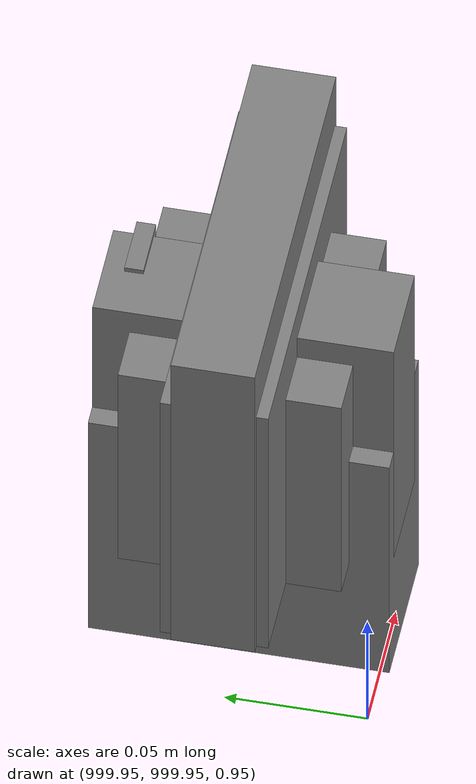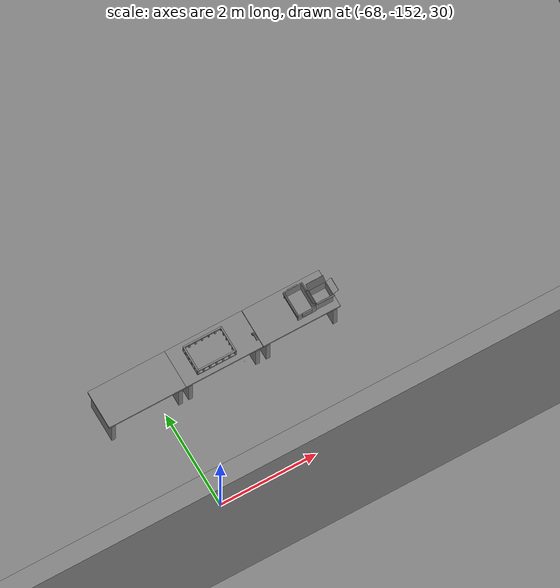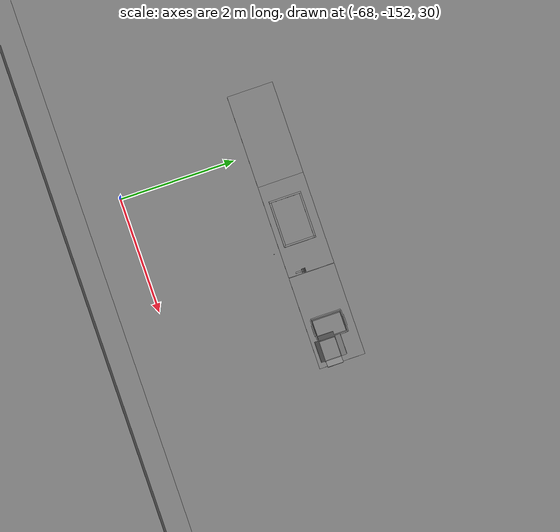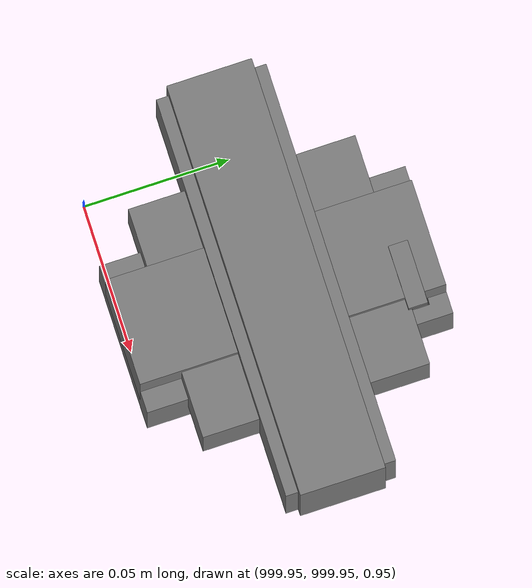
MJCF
<mujoco>
    <option gravity="0.000000000 0.000000000 -9.810000420" timestep="0.0049999999" integrator="implicitfast" density="1.225" viscosity="1.8000001e-05" noslip_iterations="10" iterations="100" sdf_iterations="50">
        <flag multiccd="disable"/>
    </option>
    <size memory="1000M"/>
    <compiler coordinate="local"/>
    <worldbody>
        <light cutoff="30" pos="0 1 1" dir="0 -1 -2"/>
        <light cutoff="30" pos="0 -1 1" dir="0 1 -2"/>
        <body pos="-64.866622925 -149.383972168 30.183746338" euler="89.999984741 89.999946594 0.000000000" name="openloong_gripper_2f85_fix_base_usda_bluebox_01">
            <geom contype="1" conaffinity="1" density="1000" type="box" material="" rgba="0.500000000 0.500000000 0.500000000 1.000000000" solimp="0.899999976 0.949999988 0.001000000" friction="1.000000000 0.005000000 0.000100000" solref="0.020000000 1.000000000" margin="0" condim="3" group="0" pos="0.276580811 0.187225342 0.000068665" quat="0.707106948 0.000077471 0.707106352 0.000077486" size="0.100000001 0.057999998 0.010000000" name="openloong_gripper_2f85_fix_base_usda_geom_59045758_E7FE_40FA_9735_4013C2D7248B"/>
            <geom contype="1" conaffinity="1" density="1000" type="box" material="" rgba="0.500000000 0.500000000 0.500000000 1.000000000" solimp="0.899999976 0.949999988 0.001000000" friction="1.000000000 0.005000000 0.000100000" solref="0.020000000 1.000000000" margin="0" condim="3" group="0" pos="0.000000000 0.002883911 0.000000000" quat="0.999999881 0.000000000 0.000000000 0.000000000" size="0.254000008 0.003000000 0.172000006" name="openloong_gripper_2f85_fix_base_usda_geom_0DAD82A7_C1AE_4024_A025_4F28380A84B1"/>
            <geom contype="1" conaffinity="1" density="1000" type="box" material="" rgba="0.500000000 0.500000000 0.500000000 1.000000000" solimp="0.899999976 0.949999988 0.001000000" friction="1.000000000 0.005000000 0.000100000" solref="0.020000000 1.000000000" margin="0" condim="3" group="0" pos="0.000000000 0.124874115 0.173484802" quat="0.999796331 0.020176515 -0.000000015 0.000000030" size="0.259999990 0.119999997 0.007000000" name="openloong_gripper_2f85_fix_base_usda_geom_032334B1_9D03_46C0_AA1C_4F7C20BF02B6"/>
            <geom contype="1" conaffinity="1" density="1000" type="box" material="" rgba="0.500000000 0.500000000 0.500000000 1.000000000" solimp="0.899999976 0.949999988 0.001000000" friction="1.000000000 0.005000000 0.000100000" solref="0.020000000 1.000000000" margin="0" condim="3" group="0" pos="0.000000000 0.124874115 -0.173469543" quat="0.999796331 -0.020176545 -0.000000015 0.000000000" size="0.259999990 0.119999997 0.007000000" name="openloong_gripper_2f85_fix_base_usda_geom_7D445544_970A_4478_934E_EEEA8EBFE271"/>
            <geom contype="1" conaffinity="1" density="1000" type="box" material="" rgba="0.500000000 0.500000000 0.500000000 1.000000000" solimp="0.899999976 0.949999988 0.001000000" friction="1.000000000 0.005000000 0.000100000" solref="0.020000000 1.000000000" margin="0" condim="3" group="0" pos="0.000000000 0.214008331 0.188980103" quat="0.999912977 0.013176724 0.000000015 0.000000000" size="0.259999990 0.029999999 0.012500000" name="openloong_gripper_2f85_fix_base_usda_geom_0E85E6F4_0E59_4219_8F0D_5934AEF813F3"/>
            <geom contype="1" conaffinity="1" density="1000" type="box" material="" rgba="0.500000000 0.500000000 0.500000000 1.000000000" solimp="0.899999976 0.949999988 0.001000000" friction="1.000000000 0.005000000 0.000100000" solref="0.020000000 1.000000000" margin="0" condim="3" group="0" pos="-0.258361816 0.125289917 0.001876831" quat="0.702796936 -0.020792112 0.710783124 0.020769298" size="0.189999998 0.119999997 0.009000000" name="openloong_gripper_2f85_fix_base_usda_geom_C6EFFD49_11F5_473D_B01F_FD93FEA4F5D8"/>
            <geom contype="1" conaffinity="1" density="1000" type="box" material="" rgba="0.500000000 0.500000000 0.500000000 1.000000000" solimp="0.899999976 0.949999988 0.001000000" friction="1.000000000 0.005000000 0.000100000" solref="0.020000000 1.000000000" margin="0" condim="3" group="0" pos="0.000000000 0.214008331 -0.188980103" quat="0.999912977 -0.013176769 0.000000030 0.000000015" size="0.259999990 0.029999999 0.012500000" name="openloong_gripper_2f85_fix_base_usda_geom_6E83377F_02FC_4122_9765_141EFD40A132"/>
            <geom contype="1" conaffinity="1" density="1000" type="box" material="" rgba="0.500000000 0.500000000 0.500000000 1.000000000" solimp="0.899999976 0.949999988 0.001000000" friction="1.000000000 0.005000000 0.000100000" solref="0.020000000 1.000000000" margin="0" condim="3" group="0" pos="-0.276611328 0.187225342 0.000068665" quat="0.707106650 0.000077441 0.707106709 0.000077456" size="0.100000001 0.057999998 0.010000000" name="openloong_gripper_2f85_fix_base_usda_geom_BDB07C64_E51F_4B9F_B090_0AB088A6A72E"/>
            <geom contype="1" conaffinity="1" density="1000" type="box" material="" rgba="0.500000000 0.500000000 0.500000000 1.000000000" solimp="0.899999976 0.949999988 0.001000000" friction="1.000000000 0.005000000 0.000100000" solref="0.020000000 1.000000000" margin="0" condim="3" group="0" pos="0.258331299 0.125289917 0.001876831" quat="0.702851415 0.018856421 0.710823774 -0.019329369" size="0.189999998 0.119999997 0.009000000" name="openloong_gripper_2f85_fix_base_usda_geom_C3C36A89_4597_4F71_865A_DE7040D33272"/>
            <freejoint name="openloong_gripper_2f85_fix_base_usda_bluebox_01_joint"/>
            <site size="0.005000000 0.005000000 0.005000000" rgba="0.500000000 0.500000000 0.500000000 1.000000000" pos="0.000000000 0.000000000 0.000000000" quat="0.999961913 0.008726534 0.000000000 0.000000000" group="0" type="sphere" name="openloong_gripper_2f85_fix_base_usda_bluebox_01site"/>
        </body>
        <body pos="-64.496299744 -149.491867065 30.235729218" euler="0.000000000 0.000000000 89.999946594" name="openloong_gripper_2f85_fix_base_usda_cardboardbox_01">
            <geom contype="1" conaffinity="1" density="1000" type="box" material="" rgba="0.500000000 0.500000000 0.500000000 1.000000000" solimp="0.899999976 0.949999988 0.001000000" friction="1.000000000 0.005000000 0.000100000" solref="0.020000000 1.000000000" margin="0" condim="3" group="0" pos="-0.003166199 -0.004086494 0.005052090" quat="1.000000000 0.000000000 0.000000000 0.000000000" size="0.142499998 0.177500010 0.005000000" name="openloong_gripper_2f85_fix_base_usda_geom_13A38680_7A62_40CF_B934_51D00711DB51"/>
            <geom contype="1" conaffinity="1" density="1000" type="box" material="" rgba="0.500000000 0.500000000 0.500000000 1.000000000" solimp="0.899999976 0.949999988 0.001000000" friction="1.000000000 0.005000000 0.000100000" solref="0.020000000 1.000000000" margin="0" condim="3" group="0" pos="-0.003166199 0.170316696 0.150570869" quat="1.000000000 0.000000000 0.000000000 0.000000000" size="0.142499998 0.005000000 0.149999991" name="openloong_gripper_2f85_fix_base_usda_geom_D0D37141_0CBB_4DAE_B76C_E85D2D993C17"/>
            <geom contype="1" conaffinity="1" density="1000" type="box" material="" rgba="0.500000000 0.500000000 0.500000000 1.000000000" solimp="0.899999976 0.949999988 0.001000000" friction="1.000000000 0.005000000 0.000100000" solref="0.020000000 1.000000000" margin="0" condim="3" group="0" pos="-0.147399902 -0.005307198 0.150570869" quat="1.000000000 0.000000000 0.000000000 0.000000000" size="0.005000000 0.177500010 0.149999991" name="openloong_gripper_2f85_fix_base_usda_geom_1B88D1CB_F4C5_4D18_AE33_ADB8D781F535"/>
            <geom contype="1" conaffinity="1" density="1000" type="box" material="" rgba="0.500000000 0.500000000 0.500000000 1.000000000" solimp="0.899999976 0.949999988 0.001000000" friction="1.000000000 0.005000000 0.000100000" solref="0.020000000 1.000000000" margin="0" condim="3" group="0" pos="0.140275955 -0.005307198 0.150570869" quat="1.000000000 0.000000000 0.000000000 0.000000000" size="0.005000000 0.177500010 0.149999991" name="openloong_gripper_2f85_fix_base_usda_geom_C1225179_896C_4537_AF2A_75128B7669CA"/>
            <geom contype="1" conaffinity="1" density="1000" type="box" material="" rgba="0.500000000 0.500000000 0.500000000 1.000000000" solimp="0.899999976 0.949999988 0.001000000" friction="1.000000000 0.005000000 0.000100000" solref="0.020000000 1.000000000" margin="0" condim="3" group="0" pos="-0.003166199 -0.181550980 0.150570869" quat="1.000000000 0.000000000 0.000000000 0.000000000" size="0.142499998 0.005000000 0.149999991" name="openloong_gripper_2f85_fix_base_usda_geom_97A186B2_8050_4CDE_9908_F9C57046F16E"/>
            <freejoint name="openloong_gripper_2f85_fix_base_usda_cardboardbox_01_joint"/>
            <site size="0.005000000 0.005000000 0.005000000" rgba="0.500000000 0.500000000 0.500000000 1.000000000" pos="0.000000000 0.000000000 0.000000000" quat="0.999961913 0.008726535 0.000000000 0.000000000" group="0" type="sphere" name="openloong_gripper_2f85_fix_base_usda_site_48D3C0B4_121E_4000_9FF0_EEF829566BDF"/>
            <body pos="0.139160156 -0.004048347 0.301930904" euler="-179.999954224 49.383502960 179.999954224" name="openloong_gripper_2f85_fix_base_usda_A1_006">
                <geom contype="1" conaffinity="1" density="1000" type="box" material="" rgba="0.500000000 0.500000000 0.500000000 1.000000000" solimp="0.899999976 0.949999988 0.001000000" friction="1.000000000 0.005000000 0.000100000" solref="0.020000000 1.000000000" margin="0" condim="3" group="0" pos="-0.071587563 0.000009537 0.001745224" quat="0.999999881 0.000000000 0.000000000 0.000000000" size="0.071249999 0.179999992 0.002500000" name="openloong_gripper_2f85_fix_base_usda_geom_F33F61DB_9AAB_4D81_B48E_94ED6C919B66"/>
                <joint armature="0" stiffness="0.07" damping="0.0099999998" axis="0.000000 1.000000 0.000000" type="hinge" name="openloong_gripper_2f85_fix_base_usda_A1_006"/>
            </body>
            <body pos="-0.145902634 -0.004086494 0.301938057" euler="-180.000000000 -60.000011444 -180.000000000" name="openloong_gripper_2f85_fix_base_usda_A2_006">
                <geom contype="1" conaffinity="1" density="1000" type="box" material="" rgba="0.500000000 0.500000000 0.500000000 1.000000000" solimp="0.899999976 0.949999988 0.001000000" friction="1.000000000 0.005000000 0.000100000" solref="0.020000000 1.000000000" margin="0" condim="3" group="0" pos="0.071268082 0.000009537 0.002717972" quat="0.000002921 0.000000000 -0.000000030 0.999999881" size="0.071249999 0.179999992 0.002500000" name="openloong_gripper_2f85_fix_base_usda_geom_A3F7A639_3DB0_4C71_AFC0_6380F2B28A67"/>
                <joint armature="0" stiffness="0.07" damping="0.0099999998" axis="0.000000 1.000000 0.000000" type="hinge" name="openloong_gripper_2f85_fix_base_usda_A2_006"/>
            </body>
            <body pos="-0.003385544 0.175991058 0.301930904" euler="-125.858116150 -0.000004561 0.000002331" name="openloong_gripper_2f85_fix_base_usda_B2_006">
                <geom contype="1" conaffinity="1" density="1000" type="box" material="" rgba="0.500000000 0.500000000 0.500000000 1.000000000" solimp="0.899999976 0.949999988 0.001000000" friction="1.000000000 0.005000000 0.000100000" solref="0.020000000 1.000000000" margin="0" condim="3" group="0" pos="0.000009537 -0.070939064 -0.002470016" quat="0.999614120 0.027776197 -0.000000015 0.000000030" size="0.137500003 0.064999998 0.005000000" name="openloong_gripper_2f85_fix_base_usda_geom_3B3D2F33_6F79_45AE_9627_1A430906512C"/>
                <joint armature="0" stiffness="0.07" damping="0.0099999998" axis="1.000000 0.000000 0.000000" type="hinge" name="openloong_gripper_2f85_fix_base_usda_B2_006"/>
            </body>
            <body pos="-0.003385544 -0.184140205 0.301938057" euler="147.805557251 0.000000000 0.000000000" name="openloong_gripper_2f85_fix_base_usda_B1_006">
                <geom contype="1" conaffinity="1" density="1000" type="box" material="" rgba="0.500000000 0.500000000 0.500000000 1.000000000" solimp="0.899999976 0.949999988 0.001000000" friction="1.000000000 0.005000000 0.000100000" solref="0.020000000 1.000000000" margin="0" condim="3" group="0" pos="-0.000028610 0.070202351 -0.002703667" quat="0.999614179 -0.027776167 0.000000000 0.000000000" size="0.137500003 0.064999998 0.005000000" name="openloong_gripper_2f85_fix_base_usda_geom_11E8700C_8654_488C_B6E8_39CBE1C20B9E"/>
                <joint armature="0" stiffness="0.07" damping="0.0099999998" axis="1.000000 0.000000 0.000000" type="hinge" name="openloong_gripper_2f85_fix_base_usda_B1_006"/>
            </body>
        </body>
        <body pos="-65.882858276 -149.481979370 30.229999542" euler="-64.487716675 0.000000000 0.000000000" name="openloong_gripper_2f85_fix_base_usda_Barcode">
            <geom contype="1" conaffinity="1" density="1000" type="box" material="" rgba="0.500000000 0.500000000 0.500000000 1.000000000" solimp="0.899999976 0.949999988 0.001000000" friction="1.000000000 0.005000000 0.000100000" solref="0.020000000 1.000000000" margin="0" condim="3" group="0" pos="0.000000000 0.013038635 0.001419067" quat="0.000000000 0.000000000 0.000000000 1.000000119" size="0.034000002 0.010000000 0.017999999" name="openloong_gripper_2f85_fix_base_usda_geom_667A2BC0_2640_4F3C_AB91_02FE0EDE2AF4"/>
            <geom contype="1" conaffinity="1" density="1000" type="box" material="" rgba="0.500000000 0.500000000 0.500000000 1.000000000" solimp="0.899999976 0.949999988 0.001000000" friction="1.000000000 0.005000000 0.000100000" solref="0.020000000 1.000000000" margin="0" condim="3" group="0" pos="0.000000000 -0.035301208 -0.007095337" quat="0.000000000 0.000000000 -0.043619365 0.999048233" size="0.028999999 0.010000000 0.020000000" name="openloong_gripper_2f85_fix_base_usda_geom_CEB8D3E4_5DDD_4D0D_AFFA_61710BEAE0C8"/>
            <geom contype="1" conaffinity="1" density="1000" type="box" material="" rgba="0.500000000 0.500000000 0.500000000 1.000000000" solimp="0.899999976 0.949999988 0.001000000" friction="1.000000000 0.005000000 0.000100000" solref="0.020000000 1.000000000" margin="0" condim="3" group="0" pos="0.000000000 -0.043411255 -0.011749268" quat="0.922262907 0.386563420 0.000000000 0.000000000" size="0.026000001 0.010000000 0.020000000" name="openloong_gripper_2f85_fix_base_usda_geom_AE5F5FF5_8AD4_4639_B353_FCCD664C9AA7"/>
            <geom contype="1" conaffinity="1" density="1000" type="box" material="" rgba="0.500000000 0.500000000 0.500000000 1.000000000" solimp="0.899999976 0.949999988 0.001000000" friction="1.000000000 0.005000000 0.000100000" solref="0.020000000 1.000000000" margin="0" condim="3" group="0" pos="0.000000000 -0.016967773 -0.031860352" quat="0.000000000 0.000000000 0.000000000 1.000000119" size="0.008000000 0.010000000 0.013000000" name="openloong_gripper_2f85_fix_base_usda_geom_F6A6ED23_E8B5_47B3_8E6A_0C575BB97210"/>
            <geom contype="1" conaffinity="1" density="1000" type="box" material="" rgba="0.500000000 0.500000000 0.500000000 1.000000000" solimp="0.899999976 0.949999988 0.001000000" friction="1.000000000 0.005000000 0.000100000" solref="0.020000000 1.000000000" margin="0" condim="3" group="0" pos="0.000000000 -0.001869202 0.000312805" quat="0.953716993 0.300705761 0.000000000 0.000000000" size="0.032000002 0.010000000 0.018999999" name="openloong_gripper_2f85_fix_base_usda_geom_6AF7E9D9_3AA8_429D_B0A0_F289309A709B"/>
            <geom contype="1" conaffinity="1" density="1000" type="box" material="" rgba="0.500000000 0.500000000 0.500000000 1.000000000" solimp="0.899999976 0.949999988 0.001000000" friction="1.000000000 0.005000000 0.000100000" solref="0.020000000 1.000000000" margin="0" condim="3" group="0" pos="0.000000000 -0.019531250 -0.003173828" quat="0.953716993 0.300705761 0.000000000 0.000000000" size="0.030999999 0.010000000 0.020000000" name="openloong_gripper_2f85_fix_base_usda_geom_06641970_830B_42E7_A1CC_C00424DEF11B"/>
            <geom contype="1" conaffinity="1" density="1000" type="box" material="" rgba="0.500000000 0.500000000 0.500000000 1.000000000" solimp="0.899999976 0.949999988 0.001000000" friction="1.000000000 0.005000000 0.000100000" solref="0.020000000 1.000000000" margin="0" condim="3" group="0" pos="0.000000000 -0.035301208 -0.007095337" quat="0.953716993 0.300705761 0.000000000 0.000000000" size="0.028999999 0.010000000 0.020000000" name="openloong_gripper_2f85_fix_base_usda_geom_D6B7ADE6_42D6_4F4C_B9F2_95E96080EE11"/>
            <geom contype="1" conaffinity="1" density="1000" type="box" material="" rgba="0.500000000 0.500000000 0.500000000 1.000000000" solimp="0.899999976 0.949999988 0.001000000" friction="1.000000000 0.005000000 0.000100000" solref="0.020000000 1.000000000" margin="0" condim="3" group="0" pos="0.000000000 -0.042617798 -0.071121216" quat="0.000000000 0.000000000 0.000000000 1.000000119" size="0.013000000 0.021000000 0.059999999" name="openloong_gripper_2f85_fix_base_usda_geom_B09DF8CC_9E85_4CD0_A31D_834B07A5AFE4"/>
            <freejoint name="openloong_gripper_2f85_fix_base_usda_Barcode_joint"/>
            <site size="0.005000000 0.005000000 0.005000000" rgba="0.500000000 0.500000000 0.500000000 1.000000000" pos="0.000000000 0.000000000 0.000000000" quat="1.000000000 0.000000000 0.000000000 0.000000000" group="0" type="sphere" name="openloong_gripper_2f85_fix_base_usda_Barcode_site"/>
        </body>
        <body pos="-66.745018005 -149.392349243 30.184000015" euler="0.000000000 0.000000000 89.999946594" name="[22332359883848]_Basket_01">
            <geom contype="1" conaffinity="1" density="1000" type="box" material="" rgba="0.500000000 0.500000000 0.500000000 1.000000000" solimp="0.899999976 0.949999988 0.001000000" friction="1.000000000 0.005000000 0.000100000" solref="0.020000000 1.000000000" margin="0" condim="3" group="0" pos="-0.052425385 0.389207840 0.089787483" quat="0.707107008 0.000000000 0.000000000 0.707106411" size="0.014249999 0.014249999 0.059999999" name="[22332359883848]_geom_74905733_FE8E_439E_A5E8_CB632DFC3A56"/>
            <geom contype="1" conaffinity="1" density="1000" type="box" material="" rgba="0.500000000 0.500000000 0.500000000 1.000000000" solimp="0.899999976 0.949999988 0.001000000" friction="1.000000000 0.005000000 0.000100000" solref="0.020000000 1.000000000" margin="0" condim="3" group="0" pos="0.264015198 -0.133043289 0.089787483" quat="0.707107008 0.000000000 0.000000000 0.707106411" size="0.014249999 0.014249999 0.059999999" name="[22332359883848]_geom_8975BB4C_8E29_47A6_8362_B46BF6FC45F5"/>
            <geom contype="1" conaffinity="1" density="1000" type="box" material="" rgba="0.500000000 0.500000000 0.500000000 1.000000000" solimp="0.899999976 0.949999988 0.001000000" friction="1.000000000 0.005000000 0.000100000" solref="0.020000000 1.000000000" margin="0" condim="3" group="0" pos="-0.264015198 -0.265548706 0.089793205" quat="0.707107008 0.000000000 0.000000000 0.707106411" size="0.014249999 0.014249999 0.059999999" name="[22332359883848]_geom_E9A7522F_2015_4DE1_B65D_3C480C8C4C1E"/>
            <geom contype="1" conaffinity="1" density="1000" type="box" material="" rgba="0.500000000 0.500000000 0.500000000 1.000000000" solimp="0.899999976 0.949999988 0.001000000" friction="1.000000000 0.005000000 0.000100000" solref="0.020000000 1.000000000" margin="0" condim="3" group="0" pos="-0.160263062 -0.389322281 0.089793205" quat="0.707107008 0.000000000 0.000000000 0.707106411" size="0.014249999 0.014249999 0.059999999" name="[22332359883848]_geom_349018E5_E307_4592_A8AF_E2E20442FAEA"/>
            <geom contype="1" conaffinity="1" density="1000" type="box" material="" rgba="0.500000000 0.500000000 0.500000000 1.000000000" solimp="0.899999976 0.949999988 0.001000000" friction="1.000000000 0.005000000 0.000100000" solref="0.020000000 1.000000000" margin="0" condim="3" group="0" pos="0.162265778 -0.389322281 0.089787483" quat="0.707107008 0.000000000 0.000000000 0.707106411" size="0.014249999 0.014249999 0.059999999" name="[22332359883848]_geom_E4A74310_B22D_41D0_8AEB_9BBA3DBB8C95"/>
            <geom contype="1" conaffinity="1" density="1000" type="box" material="" rgba="0.500000000 0.500000000 0.500000000 1.000000000" solimp="0.899999976 0.949999988 0.001000000" friction="1.000000000 0.005000000 0.000100000" solref="0.020000000 1.000000000" margin="0" condim="3" group="0" pos="0.264015198 0.389207840 0.089787483" quat="0.707107008 0.000000000 0.000000000 0.707106411" size="0.014249999 0.014249999 0.059999999" name="[22332359883848]_geom_5BFD7CF9_B71A_427F_BDC2_80D545F6D3FE"/>
            <geom contype="1" conaffinity="1" density="1000" type="box" material="" rgba="0.500000000 0.500000000 0.500000000 1.000000000" solimp="0.899999976 0.949999988 0.001000000" friction="1.000000000 0.005000000 0.000100000" solref="0.020000000 1.000000000" margin="0" condim="3" group="0" pos="-0.264015198 -0.133043289 0.089793205" quat="0.707107008 0.000000000 0.000000000 0.707106411" size="0.014249999 0.014249999 0.059999999" name="[22332359883848]_geom_7F0070DF_8D31_4F3B_9A55_51786FC19365"/>
            <geom contype="1" conaffinity="1" density="1000" type="box" material="" rgba="0.500000000 0.500000000 0.500000000 1.000000000" solimp="0.899999976 0.949999988 0.001000000" friction="1.000000000 0.005000000 0.000100000" solref="0.020000000 1.000000000" margin="0" condim="3" group="0" pos="-0.264026642 0.269256592 0.089793205" quat="0.707107008 0.000000000 0.000000000 0.707106411" size="0.014249999 0.014249999 0.059999999" name="[22332359883848]_geom_F16C4011_B918_43D6_9AD2_A2F2F285B98D"/>
            <geom contype="1" conaffinity="1" density="1000" type="box" material="" rgba="0.500000000 0.500000000 0.500000000 1.000000000" solimp="0.899999976 0.949999988 0.001000000" friction="1.000000000 0.005000000 0.000100000" solref="0.020000000 1.000000000" margin="0" condim="3" group="0" pos="0.054462433 0.389207840 0.089787483" quat="0.707107008 0.000000000 0.000000000 0.707106411" size="0.014249999 0.014249999 0.059999999" name="[22332359883848]_geom_1E53786C_2E33_4318_BF85_7BA64C545B29"/>
            <geom contype="1" conaffinity="1" density="1000" type="box" material="" rgba="0.500000000 0.500000000 0.500000000 1.000000000" solimp="0.899999976 0.949999988 0.001000000" friction="1.000000000 0.005000000 0.000100000" solref="0.020000000 1.000000000" margin="0" condim="3" group="0" pos="0.054462433 -0.389322281 0.089787483" quat="0.707107008 0.000000000 0.000000000 0.707106411" size="0.014249999 0.014249999 0.059999999" name="[22332359883848]_geom_63879E34_A0F1_42FE_8622_A4869824417F"/>
            <geom contype="1" conaffinity="1" density="1000" type="box" material="" rgba="0.500000000 0.500000000 0.500000000 1.000000000" solimp="0.899999976 0.949999988 0.001000000" friction="1.000000000 0.005000000 0.000100000" solref="0.020000000 1.000000000" margin="0" condim="3" group="0" pos="0.264015198 0.269256592 0.089793205" quat="0.707107008 0.000000000 0.000000000 0.707106411" size="0.014249999 0.014249999 0.059999999" name="[22332359883848]_geom_D322A835_72AC_4355_BB2F_EAB84C448CFA"/>
            <geom contype="1" conaffinity="1" density="1000" type="box" material="" rgba="0.500000000 0.500000000 0.500000000 1.000000000" solimp="0.899999976 0.949999988 0.001000000" friction="1.000000000 0.005000000 0.000100000" solref="0.020000000 1.000000000" margin="0" condim="3" group="0" pos="0.264015198 -0.389322281 0.089787483" quat="0.707107008 0.000000000 0.000000000 0.707106411" size="0.014249999 0.014249999 0.059999999" name="[22332359883848]_geom_C66E2343_4494_4B83_8F48_AAB278C235C3"/>
            <geom contype="1" conaffinity="1" density="1000" type="box" material="" rgba="0.500000000 0.500000000 0.500000000 1.000000000" solimp="0.899999976 0.949999988 0.001000000" friction="1.000000000 0.005000000 0.000100000" solref="0.020000000 1.000000000" margin="0" condim="3" group="0" pos="0.000000000 0.000000000 0.015998840" quat="0.707107008 0.000000000 0.000000000 0.707106411" size="0.403499991 0.279000014 0.015750000" name="[22332359883848]_geom_5AD1C46B_BB79_4130_894F_C8D15346B8B8"/>
            <geom contype="1" conaffinity="1" density="1000" type="box" material="" rgba="0.500000000 0.500000000 0.500000000 1.000000000" solimp="0.899999976 0.949999988 0.001000000" friction="1.000000000 0.005000000 0.000100000" solref="0.020000000 1.000000000" margin="0" condim="3" group="0" pos="0.000000000 -0.389476776 0.163619041" quat="0.707107008 0.000000000 0.000000000 0.707106411" size="0.015000000 0.277500004 0.015750000" name="[22332359883848]_geom_F43EE971_6767_4A1D_A99A_9590DECABD54"/>
            <geom contype="1" conaffinity="1" density="1000" type="box" material="" rgba="0.500000000 0.500000000 0.500000000 1.000000000" solimp="0.899999976 0.949999988 0.001000000" friction="1.000000000 0.005000000 0.000100000" solref="0.020000000 1.000000000" margin="0" condim="3" group="0" pos="0.162265778 0.389207840 0.089787483" quat="0.707107008 0.000000000 0.000000000 0.707106411" size="0.014249999 0.014249999 0.059999999" name="[22332359883848]_geom_188C6804_B72A_49FD_A09C_D6F606D47CBA"/>
            <geom contype="1" conaffinity="1" density="1000" type="box" material="" rgba="0.500000000 0.500000000 0.500000000 1.000000000" solimp="0.899999976 0.949999988 0.001000000" friction="1.000000000 0.005000000 0.000100000" solref="0.020000000 1.000000000" margin="0" condim="3" group="0" pos="0.000000000 0.389471054 0.163619041" quat="0.707107008 0.000000000 0.000000000 0.707106411" size="0.015000000 0.277500004 0.015750000" name="[22332359883848]_geom_8E4A3554_BCCB_413A_887E_CFA182985C45"/>
            <geom contype="1" conaffinity="1" density="1000" type="box" material="" rgba="0.500000000 0.500000000 0.500000000 1.000000000" solimp="0.899999976 0.949999988 0.001000000" friction="1.000000000 0.005000000 0.000100000" solref="0.020000000 1.000000000" margin="0" condim="3" group="0" pos="-0.263511658 0.000000000 0.163619041" quat="0.707107008 0.000000000 0.000000000 0.707106411" size="0.403499991 0.015000000 0.015750000" name="[22332359883848]_geom_61766907_C976_49FE_B8DB_2E96402DC57C"/>
            <geom contype="1" conaffinity="1" density="1000" type="box" material="" rgba="0.500000000 0.500000000 0.500000000 1.000000000" solimp="0.899999976 0.949999988 0.001000000" friction="1.000000000 0.005000000 0.000100000" solref="0.020000000 1.000000000" margin="0" condim="3" group="0" pos="-0.264015198 0.141334534 0.089793205" quat="0.707107008 0.000000000 0.000000000 0.707106411" size="0.014249999 0.014249999 0.059999999" name="[22332359883848]_geom_02B1D791_7FD4_4DF1_92F9_E5D34FE28881"/>
            <geom contype="1" conaffinity="1" density="1000" type="box" material="" rgba="0.500000000 0.500000000 0.500000000 1.000000000" solimp="0.899999976 0.949999988 0.001000000" friction="1.000000000 0.005000000 0.000100000" solref="0.020000000 1.000000000" margin="0" condim="3" group="0" pos="0.264015198 -0.265548706 0.089787483" quat="0.707107008 0.000000000 0.000000000 0.707106411" size="0.014249999 0.014249999 0.059999999" name="[22332359883848]_geom_53F8C9C2_450C_4550_B129_3AC1B0C71825"/>
            <geom contype="1" conaffinity="1" density="1000" type="box" material="" rgba="0.500000000 0.500000000 0.500000000 1.000000000" solimp="0.899999976 0.949999988 0.001000000" friction="1.000000000 0.005000000 0.000100000" solref="0.020000000 1.000000000" margin="0" condim="3" group="0" pos="-0.160263062 0.389207840 0.089787483" quat="0.707107008 0.000000000 0.000000000 0.707106411" size="0.014249999 0.014249999 0.059999999" name="[22332359883848]_geom_FF522A43_166F_4011_97EE_AC91BB2AA96B"/>
            <geom contype="1" conaffinity="1" density="1000" type="box" material="" rgba="0.500000000 0.500000000 0.500000000 1.000000000" solimp="0.899999976 0.949999988 0.001000000" friction="1.000000000 0.005000000 0.000100000" solref="0.020000000 1.000000000" margin="0" condim="3" group="0" pos="-0.052425385 -0.389322281 0.089787483" quat="0.707107008 0.000000000 0.000000000 0.707106411" size="0.014249999 0.014249999 0.059999999" name="[22332359883848]_geom_B9E2583F_516D_47A8_B894_B87BF73DF878"/>
            <geom contype="1" conaffinity="1" density="1000" type="box" material="" rgba="0.500000000 0.500000000 0.500000000 1.000000000" solimp="0.899999976 0.949999988 0.001000000" friction="1.000000000 0.005000000 0.000100000" solref="0.020000000 1.000000000" margin="0" condim="3" group="0" pos="-0.264026642 -0.389322281 0.089793205" quat="0.707107008 0.000000000 0.000000000 0.707106411" size="0.014249999 0.014249999 0.059999999" name="[22332359883848]_geom_39925629_EFBE_4877_AADE_6BD351EE26D0"/>
            <geom contype="1" conaffinity="1" density="1000" type="box" material="" rgba="0.500000000 0.500000000 0.500000000 1.000000000" solimp="0.899999976 0.949999988 0.001000000" friction="1.000000000 0.005000000 0.000100000" solref="0.020000000 1.000000000" margin="0" condim="3" group="0" pos="0.264015198 0.141334534 0.089787483" quat="0.707107008 0.000000000 0.000000000 0.707106411" size="0.014249999 0.014249999 0.059999999" name="[22332359883848]_geom_F9A550ED_E9EC_4F9C_BF59_691CF6800D47"/>
            <geom contype="1" conaffinity="1" density="1000" type="box" material="" rgba="0.500000000 0.500000000 0.500000000 1.000000000" solimp="0.899999976 0.949999988 0.001000000" friction="1.000000000 0.005000000 0.000100000" solref="0.020000000 1.000000000" margin="0" condim="3" group="0" pos="-0.264015198 0.389207840 0.089793205" quat="0.707107008 0.000000000 0.000000000 0.707106411" size="0.014249999 0.014249999 0.059999999" name="[22332359883848]_geom_B0511268_5E9B_4EAF_841E_14DB328DBC24"/>
            <geom contype="1" conaffinity="1" density="1000" type="box" material="" rgba="0.500000000 0.500000000 0.500000000 1.000000000" solimp="0.899999976 0.949999988 0.001000000" friction="1.000000000 0.005000000 0.000100000" solref="0.020000000 1.000000000" margin="0" condim="3" group="0" pos="0.264015198 0.004480362 0.089787483" quat="0.707107008 0.000000000 0.000000000 0.707106411" size="0.014249999 0.014249999 0.059999999" name="[22332359883848]_geom_9C32C0A9_FF72_4582_95EA_3C72298A3C29"/>
            <geom contype="1" conaffinity="1" density="1000" type="box" material="" rgba="0.500000000 0.500000000 0.500000000 1.000000000" solimp="0.899999976 0.949999988 0.001000000" friction="1.000000000 0.005000000 0.000100000" solref="0.020000000 1.000000000" margin="0" condim="3" group="0" pos="0.263694763 -0.000011444 0.163619041" quat="0.707107008 0.000000000 0.000000000 0.707106411" size="0.403499991 0.015000000 0.015750000" name="[22332359883848]_geom_F92556CF_5EF9_4795_A6EA_BA825E707E87"/>
            <geom contype="1" conaffinity="1" density="1000" type="box" material="" rgba="0.500000000 0.500000000 0.500000000 1.000000000" solimp="0.899999976 0.949999988 0.001000000" friction="1.000000000 0.005000000 0.000100000" solref="0.020000000 1.000000000" margin="0" condim="3" group="0" pos="-0.264015198 0.004480362 0.089793205" quat="0.707107008 0.000000000 0.000000000 0.707106411" size="0.014249999 0.014249999 0.059999999" name="[22332359883848]_geom_F6B88C69_6CC6_419B_80BD_E3D0B5075F64"/>
            <freejoint name="[22332359883848]_joint_8FFCBEB5_D75C_451F_BF01_5B485BA39B58"/>
        </body>
        <body pos="0.000000000 0.000000000 0.000000000" euler="0.000000000 0.000000000 0.000000000" name="Static Objects_Static Objects">
            <geom contype="1" conaffinity="1" density="1000" type="box" material="" rgba="0.500000000 0.500000000 0.500000000 1.000000000" solimp="0.899999976 0.949999988 0.001000000" friction="1.000000000 0.005000000 0.000100000" solref="0.020000000 1.000000000" margin="0" condim="3" group="0" pos="-67.544113159 -149.365814209 29.727830887" quat="0.500000417 0.499999970 0.499999553 0.499999970" size="0.381000012 0.319999993 0.041000001" name="Static Objects_geom_D075B509_F42D_45F1_B4F8_D7495EC5671C"/>
            <geom contype="1" conaffinity="1" density="1000" type="box" material="" rgba="0.500000000 0.500000000 0.500000000 1.000000000" solimp="0.899999976 0.949999988 0.001000000" friction="1.000000000 0.005000000 0.000100000" solref="0.020000000 1.000000000" margin="0" condim="3" group="0" pos="-68.239501953 -149.365814209 30.086868286" quat="0.500000417 0.499999970 0.499999553 0.499999970" size="0.370999992 0.039500002 0.745000005" name="Static Objects_geom_0357313A_3E71_469A_9955_09B1F0B90F53"/>
            <geom contype="1" conaffinity="1" density="1000" type="box" material="" rgba="0.500000000 0.500000000 0.500000000 1.000000000" solimp="0.899999976 0.949999988 0.001000000" friction="1.000000000 0.005000000 0.000100000" solref="0.020000000 1.000000000" margin="0" condim="3" group="0" pos="-68.239501953 -149.365814209 30.147235870" quat="0.500000417 0.499999970 0.499999553 0.499999970" size="0.400000006 0.022000000 0.800000012" name="Static Objects_geom_63176C7F_2522_48E5_9003_4FC608E445AC"/>
            <geom contype="1" conaffinity="1" density="1000" type="box" material="" rgba="0.500000000 0.500000000 0.500000000 1.000000000" solimp="0.899999976 0.949999988 0.001000000" friction="1.000000000 0.005000000 0.000100000" solref="0.020000000 1.000000000" margin="0" condim="3" group="0" pos="-68.934890747 -149.365814209 29.727830887" quat="0.500000417 0.499999970 0.499999553 0.499999970" size="0.381000012 0.319999993 0.041000001" name="Static Objects_geom_D00C5697_AD95_4019_B87E_7784D87B583F"/>
            <geom contype="1" conaffinity="1" density="1000" type="box" material="" rgba="0.500000000 0.500000000 0.500000000 1.000000000" solimp="0.899999976 0.949999988 0.001000000" friction="1.000000000 0.005000000 0.000100000" solref="0.020000000 1.000000000" margin="0" condim="3" group="0" pos="-68.239501953 -149.365814209 29.561563492" quat="0.500000417 0.499999970 0.499999553 0.499999970" size="0.020000000 0.022000000 0.660000026" name="Static Objects_geom_C16264F0_CE8F_42B5_A44A_579595DD72AA"/>
            <geom contype="1" conaffinity="1" density="1000" type="box" material="" rgba="0.500000000 0.500000000 0.500000000 1.000000000" solimp="0.899999976 0.949999988 0.001000000" friction="1.000000000 0.005000000 0.000100000" solref="0.020000000 1.000000000" margin="0" condim="3" group="0" pos="-65.945671082 -149.365814209 29.727830887" quat="0.500000417 0.499999970 0.499999553 0.499999970" size="0.381000012 0.319999993 0.041000001" name="Static Objects_geom_CEE1E256_D241_4D09_8F88_277DA97C0E1B"/>
            <geom contype="1" conaffinity="1" density="1000" type="box" material="" rgba="0.500000000 0.500000000 0.500000000 1.000000000" solimp="0.899999976 0.949999988 0.001000000" friction="1.000000000 0.005000000 0.000100000" solref="0.020000000 1.000000000" margin="0" condim="3" group="0" pos="-66.641059875 -149.365814209 30.086868286" quat="0.500000417 0.499999970 0.499999553 0.499999970" size="0.370999992 0.039500002 0.745000005" name="Static Objects_geom_185D8F3D_2BEB_47B5_901D_8B3618C6FE4B"/>
            <geom contype="1" conaffinity="1" density="1000" type="box" material="" rgba="0.500000000 0.500000000 0.500000000 1.000000000" solimp="0.899999976 0.949999988 0.001000000" friction="1.000000000 0.005000000 0.000100000" solref="0.020000000 1.000000000" margin="0" condim="3" group="0" pos="-66.641059875 -149.365814209 30.147235870" quat="0.500000417 0.499999970 0.499999553 0.499999970" size="0.400000006 0.022000000 0.800000012" name="Static Objects_geom_F2B9CD5A_4DA8_4206_9416_16E0DE63F4F2"/>
            <geom contype="1" conaffinity="1" density="1000" type="box" material="" rgba="0.500000000 0.500000000 0.500000000 1.000000000" solimp="0.899999976 0.949999988 0.001000000" friction="1.000000000 0.005000000 0.000100000" solref="0.020000000 1.000000000" margin="0" condim="3" group="0" pos="-67.336448669 -149.365814209 29.727830887" quat="0.500000417 0.499999970 0.499999553 0.499999970" size="0.381000012 0.319999993 0.041000001" name="Static Objects_geom_98AD495D_367B_4805_9C27_76FB85C50698"/>
            <geom contype="1" conaffinity="1" density="1000" type="box" material="" rgba="0.500000000 0.500000000 0.500000000 1.000000000" solimp="0.899999976 0.949999988 0.001000000" friction="1.000000000 0.005000000 0.000100000" solref="0.020000000 1.000000000" margin="0" condim="3" group="0" pos="-66.641059875 -149.365814209 29.561563492" quat="0.500000417 0.499999970 0.499999553 0.499999970" size="0.020000000 0.022000000 0.660000026" name="Static Objects_geom_9750E4C0_10D8_4E87_B67A_32739956DC69"/>
            <geom contype="1" conaffinity="1" density="1000" type="box" material="" rgba="0.500000000 0.500000000 0.500000000 1.000000000" solimp="0.899999976 0.949999988 0.001000000" friction="1.000000000 0.005000000 0.000100000" solref="0.020000000 1.000000000" margin="0" condim="3" group="0" pos="-64.338577271 -149.365814209 29.727830887" quat="0.500000417 0.499999970 0.499999553 0.499999970" size="0.381000012 0.319999993 0.041000001" name="Static Objects_geom_72A1821F_8EFB_4839_BF49_6A74513ADBDF"/>
            <geom contype="1" conaffinity="1" density="1000" type="box" material="" rgba="0.500000000 0.500000000 0.500000000 1.000000000" solimp="0.899999976 0.949999988 0.001000000" friction="1.000000000 0.005000000 0.000100000" solref="0.020000000 1.000000000" margin="0" condim="3" group="0" pos="-65.033966064 -149.365814209 30.086868286" quat="0.500000417 0.499999970 0.499999553 0.499999970" size="0.370999992 0.039500002 0.745000005" name="Static Objects_geom_536343A2_3924_417F_B3C3_21BC245985AF"/>
            <geom contype="1" conaffinity="1" density="1000" type="box" material="" rgba="0.500000000 0.500000000 0.500000000 1.000000000" solimp="0.899999976 0.949999988 0.001000000" friction="1.000000000 0.005000000 0.000100000" solref="0.020000000 1.000000000" margin="0" condim="3" group="0" pos="-65.033966064 -149.365814209 30.147235870" quat="0.500000417 0.499999970 0.499999553 0.499999970" size="0.400000006 0.022000000 0.800000012" name="Static Objects_geom_4458ACE8_2703_430E_AF49_72D380A09BEA"/>
            <geom contype="1" conaffinity="1" density="1000" type="box" material="" rgba="0.500000000 0.500000000 0.500000000 1.000000000" solimp="0.899999976 0.949999988 0.001000000" friction="1.000000000 0.005000000 0.000100000" solref="0.020000000 1.000000000" margin="0" condim="3" group="0" pos="-65.729354858 -149.365814209 29.727830887" quat="0.500000417 0.499999970 0.499999553 0.499999970" size="0.381000012 0.319999993 0.041000001" name="Static Objects_geom_C98473A1_0FC5_489D_9016_808864932CE6"/>
            <geom contype="1" conaffinity="1" density="1000" type="box" material="" rgba="0.500000000 0.500000000 0.500000000 1.000000000" solimp="0.899999976 0.949999988 0.001000000" friction="1.000000000 0.005000000 0.000100000" solref="0.020000000 1.000000000" margin="0" condim="3" group="0" pos="-65.033966064 -149.365814209 29.561563492" quat="0.500000417 0.499999970 0.499999553 0.499999970" size="0.020000000 0.022000000 0.660000026" name="Static Objects_geom_92F03276_31C6_431F_8699_2C740DF15ACA"/>
            <geom contype="1" conaffinity="1" density="1000" type="box" material="" rgba="0.500000000 0.500000000 0.500000000 1.000000000" solimp="0.899999976 0.949999988 0.001000000" friction="1.000000000 0.005000000 0.000100000" solref="0.020000000 1.000000000" margin="0" condim="3" group="0" pos="-61.754566193 -137.853729248 33.906845093" quat="0.707107067 0.000000000 0.000000000 0.707106471" size="0.759999990 0.759999990 4.500000000" name="Static Objects_geom_2AA8DC93_82C7_42B2_8833_7333693B888C"/>
            <geom contype="1" conaffinity="1" density="1000" type="box" material="" rgba="0.500000000 0.500000000 0.500000000 1.000000000" solimp="0.899999976 0.949999988 0.001000000" friction="1.000000000 0.005000000 0.000100000" solref="0.020000000 1.000000000" margin="0" condim="3" group="0" pos="-57.511135101 -144.927108765 31.707921982" quat="1.000000000 0.000000000 0.000000000 0.000000000" size="0.200000003 8.000000000 2.299999952" name="Static Objects_geom_85FB8442_9AC1_473C_8F16_FA80196CD54D"/>
            <geom contype="1" conaffinity="1" density="1000" type="box" material="" rgba="0.500000000 0.500000000 0.500000000 1.000000000" solimp="0.899999976 0.949999988 0.001000000" friction="1.000000000 0.005000000 0.000100000" solref="0.020000000 1.000000000" margin="0" condim="3" group="0" pos="-80.517646790 -157.574050903 31.688196182" quat="0.707107067 0.000000000 0.000000000 0.707106471" size="0.600000024 0.600000024 2.299999952" name="Static Objects_geom_5C653CBA_E01B_4607_83D6_266BB27FEB35"/>
            <geom contype="1" conaffinity="1" density="1000" type="box" material="" rgba="0.500000000 0.500000000 0.500000000 1.000000000" solimp="0.899999976 0.949999988 0.001000000" friction="1.000000000 0.005000000 0.000100000" solref="0.020000000 1.000000000" margin="0" condim="3" group="0" pos="-80.711044312 -147.414932251 31.666158676" quat="1.000000000 0.000000000 0.000000000 0.000000000" size="0.200000003 10.000000000 2.299999952" name="Static Objects_geom_A618F919_07A6_4BEB_A1AA_1EA667B22AB4"/>
            <geom contype="1" conaffinity="1" density="1000" type="box" material="" rgba="0.500000000 0.500000000 0.500000000 1.000000000" solimp="0.899999976 0.949999988 0.001000000" friction="1.000000000 0.005000000 0.000100000" solref="0.020000000 1.000000000" margin="0" condim="3" group="0" pos="-57.687217712 -137.434692383 31.688196182" quat="0.707107067 0.000000000 0.000000000 0.707106471" size="0.600000024 0.600000024 2.299999952" name="Static Objects_geom_11ABFD49_3119_4299_AEE3_3E30DBFAF8B9"/>
            <geom contype="1" conaffinity="1" density="1000" type="box" material="" rgba="0.500000000 0.500000000 0.500000000 1.000000000" solimp="0.899999976 0.949999988 0.001000000" friction="1.000000000 0.005000000 0.000100000" solref="0.020000000 1.000000000" margin="0" condim="3" group="0" pos="-69.537033081 -140.263229370 31.714921951" quat="0.707107067 0.000000000 0.000000000 0.707106471" size="0.759999990 4.500000000 2.299999952" name="Static Objects_geom_7A3B463C_210D_4C8C_9AE5_F2D97DDC0B3C"/>
            <geom contype="1" conaffinity="1" density="1000" type="box" material="" rgba="0.500000000 0.500000000 0.500000000 1.000000000" solimp="0.899999976 0.949999988 0.001000000" friction="1.000000000 0.005000000 0.000100000" solref="0.020000000 1.000000000" margin="0" condim="3" group="0" pos="-80.073638916 -137.853713989 33.906845093" quat="0.707107067 0.000000000 0.000000000 0.707106471" size="0.759999990 0.759999990 4.500000000" name="Static Objects_geom_0E54D5B8_8DD7_4705_8AC3_CA528C9B4DFF"/>
            <geom contype="1" conaffinity="1" density="1000" type="box" material="" rgba="0.500000000 0.500000000 0.500000000 1.000000000" solimp="0.899999976 0.949999988 0.001000000" friction="1.000000000 0.005000000 0.000100000" solref="0.020000000 1.000000000" margin="0" condim="3" group="0" pos="-73.406707764 -155.734664917 31.707921982" quat="1.000000000 0.000000000 0.000000000 0.000000000" size="0.200000003 3.000000000 2.299999952" name="Static Objects_geom_8D3DA807_64F3_4FB0_AC41_AAD8D22535A8"/>
            <geom contype="1" conaffinity="1" density="1000" type="box" material="" rgba="0.500000000 0.500000000 0.500000000 1.000000000" solimp="0.899999976 0.949999988 0.001000000" friction="1.000000000 0.005000000 0.000100000" solref="0.020000000 1.000000000" margin="0" condim="3" group="0" pos="-68.497543335 -137.448257446 31.707921982" quat="0.707107067 0.000000000 0.000000000 0.707106471" size="0.200000003 14.000000000 2.299999952" name="Static Objects_geom_3B85631D_6D5C_4AF8_94EF_3AF4A2E95933"/>
            <geom contype="1" conaffinity="1" density="1000" type="cylinder" material="" rgba="0.500000000 0.500000000 0.500000000 1.000000000" solimp="0.899999976 0.949999988 0.001000000" friction="1.000000000 0.005000000 0.000100000" solref="0.020000000 1.000000000" margin="0" condim="3" group="0" pos="-68.868522644 -142.134506226 31.711090088" quat="0.707107067 0.000000000 0.000000000 0.707106471" size="0.509999990 2.299999952 1.000000000" name="Static Objects_geom_D66AF3AE_62DB_46A6_9A65_63CAEF9A24E6"/>
            <geom contype="1" conaffinity="1" density="1000" type="plane" material="" rgba="0.500000000 0.500000000 0.500000000 1.000000000" solimp="0.899999976 0.949999988 0.001000000" friction="1.000000000 0.005000000 0.000100000" solref="0.020000000 1.000000000" margin="0" condim="3" group="0" pos="-72.873703003 -147.131927490 29.409669876" quat="1.000000000 0.000000000 0.000000000 0.000000000" size="18.000000000 14.000000000 1.000000000" name="Static Objects_geom_960DC4D9_5C19_48E3_81B2_6BE11C108EA2"/>
            <geom contype="1" conaffinity="1" density="1000" type="box" material="" rgba="0.500000000 0.500000000 0.500000000 1.000000000" solimp="0.899999976 0.949999988 0.001000000" friction="1.000000000 0.005000000 0.000100000" solref="0.020000000 1.000000000" margin="0" condim="3" group="0" pos="-79.943580627 -157.782272339 31.707921982" quat="0.707107067 0.000000000 0.000000000 0.707106471" size="0.200000003 7.000000000 2.299999952" name="Static Objects_geom_CB0294E7_C681_40A6_B0DB_554E8378B2AE"/>
            <geom contype="1" conaffinity="1" density="1000" type="box" material="" rgba="0.500000000 0.500000000 0.500000000 1.000000000" solimp="0.899999976 0.949999988 0.001000000" friction="1.000000000 0.005000000 0.000100000" solref="0.020000000 1.000000000" margin="0" condim="3" group="0" pos="-65.421028137 -152.903442383 31.707921982" quat="0.707107067 0.000000000 0.000000000 0.707106471" size="0.200000003 7.800000191 2.299999952" name="Static Objects_geom_CF527D81_DA0B_4A1D_A94A_C2932712DEF2"/>
            <geom contype="1" conaffinity="1" density="1000" type="box" material="" rgba="0.500000000 0.500000000 0.500000000 1.000000000" solimp="0.899999976 0.949999988 0.001000000" friction="1.000000000 0.005000000 0.000100000" solref="0.020000000 1.000000000" margin="0" condim="3" group="0" pos="-74.776908875 -149.964416504 31.688196182" quat="1.000000000 0.000000000 0.000000000 0.000000000" size="0.600000024 0.409999996 2.299999952" name="Static Objects_geom_AADE6698_4201_4946_935A_C0B44F2F4AB9"/>
            <geom contype="1" conaffinity="1" density="1000" type="cylinder" material="" rgba="0.500000000 0.500000000 0.500000000 1.000000000" solimp="0.899999976 0.949999988 0.001000000" friction="1.000000000 0.005000000 0.000100000" solref="0.020000000 1.000000000" margin="0" condim="3" group="0" pos="-60.161884308 -142.134506226 31.711090088" quat="0.707107067 0.000000000 0.000000000 0.707106471" size="0.509999990 2.299999952 1.000000000" name="Static Objects_geom_D2536DD1_B650_4699_AE54_8260934E9702"/>
            <geom contype="1" conaffinity="1" density="1000" type="cylinder" material="" rgba="0.500000000 0.500000000 0.500000000 1.000000000" solimp="0.899999976 0.949999988 0.001000000" friction="1.000000000 0.005000000 0.000100000" solref="0.020000000 1.000000000" margin="0" condim="3" group="0" pos="-75.382453918 -149.963455200 31.711090088" quat="0.707107067 0.000000000 0.000000000 0.707106471" size="0.409999996 2.299999952 1.000000000" name="Static Objects_geom_3EE2BAD1_E406_4E94_BCB0_680AC668F94C"/>
            <geom contype="1" conaffinity="1" density="1000" type="cylinder" material="" rgba="0.500000000 0.500000000 0.500000000 1.000000000" solimp="0.899999976 0.949999988 0.001000000" friction="1.000000000 0.005000000 0.000100000" solref="0.020000000 1.000000000" margin="0" condim="3" group="0" pos="-74.154960632 -149.963455200 31.711090088" quat="0.707107067 0.000000000 0.000000000 0.707106471" size="0.409999996 2.299999952 1.000000000" name="Static Objects_geom_B0AC4D34_6E37_4C06_843A_865B11AC9227"/>
            <geom contype="1" conaffinity="1" density="1000" type="cylinder" material="" rgba="0.500000000 0.500000000 0.500000000 1.000000000" solimp="0.899999976 0.949999988 0.001000000" friction="1.000000000 0.005000000 0.000100000" solref="0.020000000 1.000000000" margin="0" condim="3" group="0" pos="-77.566612244 -142.134506226 31.711090088" quat="0.707107067 0.000000000 0.000000000 0.707106471" size="0.509999990 2.299999952 1.000000000" name="Static Objects_geom_1C673911_AB8B_487D_A319_1602B09526E8"/>
        </body>
        <body pos="1000.000000000 1000.000000000 1.000000000" euler="0.000000000 0.000000000 180.000000000" name="openloong_gripper_2f85_fix_base_usda_wifi_box">
            <geom contype="1" conaffinity="1" density="1000" type="box" material="" rgba="0.500000000 0.500000000 0.500000000 1.000000000" solimp="0.899999976 0.949999988 0.001000000" friction="1.000000000 0.005000000 0.000100000" solref="0.020000000 1.000000000" margin="0" condim="3" group="0" pos="0.000000000 0.000000000 0.058978677" quat="0.000000000 0.000000047 0.000000000 1.000000000" size="0.068499997 0.018999999 0.059000000" name="openloong_gripper_2f85_fix_base_usda_geom_C909A054_EF90_4169_B7F3_D0A0FF6FDC55"/>
            <freejoint name="openloong_gripper_2f85_fix_base_usda_wifi_box_joint"/>
            <site size="0.005000000 0.005000000 0.005000000" rgba="0.500000000 0.500000000 0.500000000 1.000000000" pos="0.000000000 0.000000000 0.000000000" quat="0.999961913 0.008726500 0.000000000 0.000000000" group="0" type="sphere" name="openloong_gripper_2f85_fix_base_usda_wifi_boxsite"/>
        </body>
        <body pos="-66.393882751 -149.270126343 31.168720245" euler="25.673551559 42.591518402 135.214401245" mocap="true" name="spotlight6_SpotLight"/>
        <body pos="1000.000000000 1000.000000000 1.000000000" euler="0.000011953 0.000005123 -179.999984741" name="openloong_gripper_2f85_fix_base_usda_intel_box">
            <geom contype="1" conaffinity="1" density="1000" type="box" material="" rgba="0.500000000 0.500000000 0.500000000 1.000000000" solimp="0.899999976 0.949999988 0.001000000" friction="1.000000000 0.005000000 0.000100000" solref="0.020000000 1.000000000" margin="0" condim="3" group="0" pos="0.000000000 -0.000067139 0.000082284" quat="0.707106709 0.000000225 0.000000253 0.707106650" size="0.052800003 0.025300000 0.052800003" name="openloong_gripper_2f85_fix_base_usda_geom_540A3DC9_DD77_469F_A247_74F52AD191E2"/>
            <freejoint name="openloong_gripper_2f85_fix_base_usda_intel_box_joint"/>
            <site size="0.005000000 0.005000000 0.005000000" rgba="0.500000000 0.500000000 0.500000000 1.000000000" pos="0.000000000 0.000000000 0.000000000" quat="0.999961913 0.008726500 0.000000000 0.000000000" group="0" type="sphere" name="openloong_gripper_2f85_fix_base_usda_intel_boxsite"/>
        </body>
        <body pos="-66.099044800 -149.261871338 31.170886993" euler="-11.402019501 -61.101222992 161.966140747" mocap="true" name="spotlight5_SpotLight"/>
        <body pos="1000.000000000 999.999938965 1.000000000" euler="0.000000000 0.000000000 180.000000000" name="openloong_gripper_2f85_fix_base_usda_intelcore_i5">
            <geom contype="1" conaffinity="1" density="1000" type="box" material="" rgba="0.500000000 0.500000000 0.500000000 1.000000000" solimp="0.899999976 0.949999988 0.001000000" friction="1.000000000 0.005000000 0.000100000" solref="0.020000000 1.000000000" margin="0" condim="3" group="0" pos="0.000000000 0.000000000 0.051722717" quat="0.707106709 0.000000000 0.000000000 -0.707106769" size="0.052800000 0.018080002 0.052800000" name="openloong_gripper_2f85_fix_base_usda_geom_ABB0C3F8_BA6F_4438_9501_4BEFC0A8C70D"/>
            <freejoint name="openloong_gripper_2f85_fix_base_usda_intelcore_i5_joint"/>
            <site size="0.005000000 0.005000000 0.005000000" rgba="0.500000000 0.500000000 0.500000000 1.000000000" pos="0.000000000 0.000000000 0.000000000" quat="0.999961913 0.008726534 0.000000000 0.000000000" group="0" type="sphere" name="openloong_gripper_2f85_fix_base_usda_intelcore_i5site"/>
        </body>
        <body pos="1000.000000000 1000.000000000 1.000000000" euler="0.000000000 0.000000000 180.000000000" name="openloong_gripper_2f85_fix_base_usda_cpu_fan">
            <geom contype="1" conaffinity="1" density="1000" type="box" material="" rgba="0.500000000 0.500000000 0.500000000 1.000000000" solimp="0.899999976 0.949999988 0.001000000" friction="1.000000000 0.005000000 0.000100000" solref="0.020000000 1.000000000" margin="0" condim="3" group="0" pos="0.000000000 0.000000000 0.070034981" quat="0.000000000 0.000000000 0.000000000 1.000000000" size="0.070700005 0.014699999 0.070700005" name="openloong_gripper_2f85_fix_base_usda_geom_27D0A151_0B59_4C99_8CD1_24E59ABC53C1"/>
            <freejoint name="openloong_gripper_2f85_fix_base_usda_cpu_fan_joint"/>
            <site size="0.005000000 0.005000000 0.005000000" rgba="0.500000000 0.500000000 0.500000000 1.000000000" pos="0.000000000 0.000000000 0.000000000" quat="0.999961913 0.008726535 0.000000000 0.000000000" group="0" type="sphere" name="openloong_gripper_2f85_fix_base_usda_cpu_fancsite"/>
        </body>
        <body pos="1000.000000000 1000.000000000 1.000000000" euler="0.000000000 0.000000000 180.000000000" name="openloong_gripper_2f85_fix_base_usda_battery_01">
            <geom contype="1" conaffinity="1" density="1000" type="box" material="" rgba="0.500000000 0.500000000 0.500000000 1.000000000" solimp="0.899999976 0.949999988 0.001000000" friction="1.000000000 0.005000000 0.000100000" solref="0.020000000 1.000000000" margin="0" condim="3" group="0" pos="-0.011123657 -0.041940309 0.101691343" quat="1.000000000 0.000000000 0.000000000 0.000000000" size="0.010800000 0.003375000 0.004725000" name="openloong_gripper_2f85_fix_base_usda_geom_8C8EEE88_4C01_4C6B_A6EF_0317037D02FD"/>
            <geom contype="1" conaffinity="1" density="1000" type="box" material="" rgba="0.500000000 0.500000000 0.500000000 1.000000000" solimp="0.899999976 0.949999988 0.001000000" friction="1.000000000 0.005000000 0.000100000" solref="0.020000000 1.000000000" margin="0" condim="3" group="0" pos="-0.010876465 -0.044247437 0.047066893" quat="0.998702705 -0.050920475 0.000000000 0.000000000" size="0.009450001 0.002700000 0.024975000" name="openloong_gripper_2f85_fix_base_usda_geom_FC423FA0_F020_41DD_BCB1_4862149E9952"/>
            <geom contype="1" conaffinity="1" density="1000" type="box" material="" rgba="0.500000000 0.500000000 0.500000000 1.000000000" solimp="0.899999976 0.949999988 0.001000000" friction="1.000000000 0.005000000 0.000100000" solref="0.020000000 1.000000000" margin="0" condim="3" group="0" pos="-0.001235962 -0.000659180 0.047381196" quat="1.000000000 0.000000000 0.000000000 0.000000000" size="0.039420001 0.039150000 0.047250003" name="openloong_gripper_2f85_fix_base_usda_geom_D829529C_37A1_4649_9F48_74A26780A8EB"/>
            <geom contype="1" conaffinity="1" density="1000" type="box" material="" rgba="0.500000000 0.500000000 0.500000000 1.000000000" solimp="0.899999976 0.949999988 0.001000000" friction="1.000000000 0.005000000 0.000100000" solref="0.020000000 1.000000000" margin="0" condim="3" group="0" pos="-0.010876465 -0.039138794 0.009851727" quat="1.000000000 0.000000000 0.000000000 0.000000000" size="0.009450001 0.010800000 0.013500000" name="openloong_gripper_2f85_fix_base_usda_geom_1D279383_261F_428E_BA90_8B8BC00C23FA"/>
            <geom contype="1" conaffinity="1" density="1000" type="box" material="" rgba="0.500000000 0.500000000 0.500000000 1.000000000" solimp="0.899999976 0.949999988 0.001000000" friction="1.000000000 0.005000000 0.000100000" solref="0.020000000 1.000000000" margin="0" condim="3" group="0" pos="-0.010876465 -0.041528322 0.071508206" quat="1.000000000 0.000000000 0.000000000 0.000000000" size="0.009450001 0.002700000 0.027000001" name="openloong_gripper_2f85_fix_base_usda_geom_E245BFB7_1711_4033_9FD3_7CAC4D04DB99"/>
            <freejoint name="openloong_gripper_2f85_fix_base_usda_battery_01_joint"/>
            <site size="0.005000000 0.005000000 0.005000000" rgba="0.500000000 0.500000000 0.500000000 1.000000000" pos="0.000000000 0.000000000 0.000000000" quat="0.999961913 0.008726500 0.000000000 0.000000000" group="0" type="sphere" name="openloong_gripper_2f85_fix_base_usda_battery_01site"/>
        </body>
        <body pos="-66.272140503 -149.770294189 31.170709610" euler="0.931105733 -82.502677917 90.637596130" mocap="true" name="spotlight4_SpotLight"/>
        <body pos="-66.291030884 -149.869689941 29.018842697" euler="0.000000000 0.000000000 89.999946594" mocap="true" name="openloong_gripper_2f85_fix_base_usda_leftHandMocap"/>
        <body pos="-66.291030884 -149.869689941 29.018842697" euler="0.000000000 0.000000000 89.999946594" mocap="true" name="openloong_gripper_2f85_fix_base_usda_rightHandMocap"/>
        <body pos="-66.291030884 -149.869689941 30.218843460" euler="0.000000000 0.000000000 89.999946594" name="openloong_gripper_2f85_fix_base_usda_base_link">
            <geom contype="1" conaffinity="1" density="1000" type="mesh" material="" rgba="0.783999979 0.783999979 0.783999979 1.000000000" solimp="0.899999976 0.949999988 0.001000000" friction="1.000000000 0.005000000 0.000100000" solref="0.020000000 1.000000000" margin="0" condim="3" group="3" mesh="base_link" pos="0.000000000 0.000000000 0.000000000" quat="1.000000000 0.000000000 0.000000000 0.000000000" size="1.000000000 1.000000000 1.000000000" name="openloong_gripper_2f85_fix_base_usda__geom_7_F5EF8629_F648_47A7_A215_86EE40E716A8"/>
            <site size="0.005000000 0.005000000 0.005000000" rgba="0.500000000 0.500000000 0.500000000 1.000000000" pos="0.000000000 0.000000000 0.000000000" quat="1.000000000 0.000000000 0.000000000 0.000000000" group="0" type="sphere" name="openloong_gripper_2f85_fix_base_usda_imu"/>
            <inertial mass="22.447001" pos="-0.005664100 -0.001336700 0.238289997" diaginertia="0.374352545 0.277180195 0.220617250" quat="0.999247074 0.035235517 -0.015086859 0.006023135"/>
            <body pos="0.000000000 0.000000000 0.299997330" euler="0.000000000 0.000000000 0.000000000" name="openloong_gripper_2f85_fix_base_usda_dummy_body">
                <geom contype="1" conaffinity="1" density="1000" type="sphere" material="" rgba="0.783999979 0.783999979 0.783999979 1.000000000" solimp="0.899999976 0.949999988 0.001000000" friction="1.000000000 0.005000000 0.000100000" solref="0.020000000 1.000000000" margin="0" condim="3" group="3" pos="0.000000000 0.000000000 0.000000000" quat="1.000000000 0.000000000 0.000000000 0.000000000" size="0.010000000 0.000000000 0.000000000" name="openloong_gripper_2f85_fix_base_usda__geom_8_65AC81C5_1663_426E_9D40_F229B9E709F2"/>
                <joint armature="0.0099999998" stiffness="0" damping="0.1" axis="0.000000 0.000000 1.000000" type="hinge" name="openloong_gripper_2f85_fix_base_usda_dummy_joint"/>
                <site size="0.010000000 0.005000000 0.005000000" rgba="0.500000000 0.500000000 0.500000000 1.000000000" pos="0.000000000 0.000000000 0.000000000" quat="1.000000000 0.000000000 0.000000000 0.000000000" group="3" type="sphere" name="openloong_gripper_2f85_fix_base_usda_dummy_site"/>
            </body>
            <body pos="0.009002686 0.000000000 0.406400681" euler="0.000000000 0.000000000 0.000000000" name="openloong_gripper_2f85_fix_base_usda_Link_head_yaw">
                <geom contype="1" conaffinity="1" density="1000" type="mesh" material="" rgba="0.783999979 0.783999979 0.783999979 1.000000000" solimp="0.899999976 0.949999988 0.001000000" friction="1.000000000 0.005000000 0.000100000" solref="0.020000000 1.000000000" margin="0" condim="3" group="3" mesh="Link_head_yaw" pos="0.000000000 0.000000000 0.000000000" quat="1.000000000 0.000000000 0.000000000 0.000000000" size="1.000000000 1.000000000 1.000000000" name="openloong_gripper_2f85_fix_base_usda__geom_10_27A57E7D_79CE_4037_A837_EE84254B564D"/>
                <inertial mass="0.84249002" pos="0.000000000 -0.002081400 0.044801001" diaginertia="0.000700588 0.000629000 0.000553812" quat="0.706933022 -0.015675601 0.015677100 0.706933022"/>
                <body pos="0.000000000 -0.034599304 0.048500061" euler="0.000000000 0.000000000 0.000000000" name="openloong_gripper_2f85_fix_base_usda_Link_head_pitch">
                    <geom contype="1" conaffinity="1" density="1000" type="mesh" material="" rgba="0.783999979 0.783999979 0.783999979 1.000000000" solimp="0.899999976 0.949999988 0.001000000" friction="1.000000000 0.005000000 0.000100000" solref="0.020000000 1.000000000" margin="0" condim="3" group="3" mesh="Link_head_pitch" pos="0.000000000 0.000000000 0.000000000" quat="1.000000000 0.000000000 0.000000000 0.000000000" size="1.000000000 1.000000000 1.000000000" name="openloong_gripper_2f85_fix_base_usda__geom_12_3548691E_FDCE_49EE_B435_FCC3658A1055"/>
                    <inertial mass="1.3943" pos="0.020569000 0.033004001 0.125000000" diaginertia="0.006381400 0.006289940 0.004481460" quat="0.973390222 0.008406822 0.228157058 0.019624906"/>
                    <body pos="0.000000000 0.029998779 0.000000000" euler="0.000000000 0.000000000 0.000000000" name="openloong_gripper_2f85_fix_base_usda_neck_center_body">
                        <site size="0.010000000 0.005000000 0.005000000" rgba="0.500000000 0.500000000 0.500000000 1.000000000" pos="0.000000000 0.000000000 0.000000000" quat="1.000000000 0.000000000 0.000000000 0.000000000" group="3" type="sphere" name="openloong_gripper_2f85_fix_base_usda_neck_center_site"/>
                        <body pos="0.020004272 0.000000000 0.149999619" euler="-0.000002229 39.998176575 -90.000205994" name="openloong_gripper_2f85_fix_base_usda_camera_head">
                            <site size="0.010000000 0.005000000 0.005000000" rgba="0.500000000 0.500000000 0.500000000 1.000000000" pos="0.000000000 0.000000000 0.000000000" quat="1.000000000 0.000000000 0.000000000 0.000000000" group="3" type="sphere" name="openloong_gripper_2f85_fix_base_usda_camera_head_site"/>
                        </body>
                    </body>
                </body>
            </body>
            <body pos="0.003997803 -0.161598206 0.392200470" euler="0.000000000 0.000000000 0.000000000" name="openloong_gripper_2f85_fix_base_usda_Link_arm_r_01">
                <geom contype="1" conaffinity="1" density="1000" type="mesh" material="" rgba="0.783999979 0.783999979 0.783999979 1.000000000" solimp="0.899999976 0.949999988 0.001000000" friction="1.000000000 0.005000000 0.000100000" solref="0.020000000 1.000000000" margin="0" condim="3" group="3" mesh="Link_arm_r_01" pos="0.000000000 0.000000000 0.000000000" quat="1.000000000 0.000000000 0.000000000 0.000000000" size="1.000000000 1.000000000 1.000000000" name="openloong_gripper_2f85_fix_base_usda__geom_14_6F586430_E7C3_4544_9AC5_221D0B4DD2A6"/>
                <joint armature="0.0099999998" stiffness="0" damping="1" axis="0.000000 -1.000000 0.000000" limited="true" range="-170.000015259 170.000015259" type="hinge" name="openloong_gripper_2f85_fix_base_usda_J_arm_r_01"/>
                <inertial mass="0.75641" pos="0.004494600 -0.038293999 -0.000001874" diaginertia="0.000842990 0.000803050 0.000587120" quat="-0.000163502 0.707098067 0.000812463 0.707115054"/>
                <body pos="-0.041992188 -0.041000366 0.000000000" euler="0.000000000 0.000000000 0.000000000" name="openloong_gripper_2f85_fix_base_usda_Link_arm_r_02">
                    <geom contype="1" conaffinity="1" density="1000" type="mesh" material="" rgba="0.783999979 0.783999979 0.783999979 1.000000000" solimp="0.899999976 0.949999988 0.001000000" friction="1.000000000 0.005000000 0.000100000" solref="0.020000000 1.000000000" margin="0" condim="3" group="3" mesh="Link_arm_r_02" pos="0.000000000 0.000000000 0.000000000" quat="1.000000000 0.000000000 0.000000000 0.000000000" size="1.000000000 1.000000000 1.000000000" name="openloong_gripper_2f85_fix_base_usda__geom_16_B3033BBD_D694_4652_8811_7AC3D8989A61"/>
                    <joint armature="0.0099999998" stiffness="0" damping="1" axis="-1.000000 0.000000 0.000000" limited="true" range="-105.000244141 105.000244141" type="hinge" name="openloong_gripper_2f85_fix_base_usda_J_arm_r_02"/>
                    <inertial mass="0.98500001" pos="0.041999999 -0.067430697 0.000000000" diaginertia="0.002262690 0.001730990 0.001154020" quat="0.500000000 0.500000000 -0.500000000 0.500000000"/>
                    <body pos="0.041992188 -0.122596741 0.000000000" euler="0.000000000 0.000000000 0.000000000" name="openloong_gripper_2f85_fix_base_usda_Link_arm_r_03">
                        <geom contype="1" conaffinity="1" density="1000" type="mesh" material="" rgba="0.783999979 0.783999979 0.783999979 1.000000000" solimp="0.899999976 0.949999988 0.001000000" friction="1.000000000 0.005000000 0.000100000" solref="0.020000000 1.000000000" margin="0" condim="3" group="3" mesh="Link_arm_r_03" pos="0.000000000 0.000000000 0.000000000" quat="1.000000000 0.000000000 0.000000000 0.000000000" size="1.000000000 1.000000000 1.000000000" name="openloong_gripper_2f85_fix_base_usda__geom_18_2C3F30E0_B911_4E7E_9834_0D2125A714AF"/>
                        <joint armature="0.0099999998" stiffness="0" damping="1" axis="0.000000 -1.000000 0.000000" limited="true" range="-170.000015259 170.000015259" type="hinge" name="openloong_gripper_2f85_fix_base_usda_J_arm_r_03"/>
                        <inertial mass="0.95899999" pos="-0.001413580 -0.164663002 0.020757901" diaginertia="0.002101340 0.002064590 0.000754802" quat="0.560480952 0.454391927 -0.443732947 0.531497955"/>
                        <body pos="0.035293579 -0.177406311 0.023998260" euler="0.000000000 0.000000000 0.000000000" name="openloong_gripper_2f85_fix_base_usda_Link_arm_r_04">
                            <geom contype="1" conaffinity="1" density="1000" type="mesh" material="" rgba="0.783999979 0.783999979 0.783999979 1.000000000" solimp="0.899999976 0.949999988 0.001000000" friction="1.000000000 0.005000000 0.000100000" solref="0.020000000 1.000000000" margin="0" condim="3" group="3" mesh="Link_arm_r_04" pos="0.000000000 0.000000000 0.000000000" quat="1.000000000 0.000000000 0.000000000 0.000000000" size="1.000000000 1.000000000 1.000000000" name="openloong_gripper_2f85_fix_base_usda__geom_20_5384B99D_767F_43A9_8579_0CD925EF4D78"/>
                            <joint armature="0.0099999998" stiffness="0" damping="1" axis="-1.000000 0.000000 0.000000" limited="true" range="0.000000000 170.000015259" type="hinge" name="openloong_gripper_2f85_fix_base_usda_J_arm_r_04"/>
                            <inertial mass="0.60000002" pos="-0.038727000 -0.060766999 -0.021003000" diaginertia="0.001092610 0.000712422 0.000645102" quat="0.327701002 0.632602990 -0.467366993 0.523443997"/>
                            <body pos="-0.035293579 -0.103492737 -0.023998260" euler="0.000000000 0.000000000 0.000000000" name="openloong_gripper_2f85_fix_base_usda_Link_arm_r_05">
                                <geom contype="1" conaffinity="1" density="1000" type="mesh" material="" rgba="0.783999979 0.783999979 0.783999979 1.000000000" solimp="0.899999976 0.949999988 0.001000000" friction="1.000000000 0.005000000 0.000100000" solref="0.020000000 1.000000000" margin="0" condim="3" group="3" mesh="Link_arm_r_05" pos="0.000000000 0.000000000 0.000000000" quat="1.000000000 0.000000000 0.000000000 0.000000000" size="1.000000000 1.000000000 1.000000000" name="openloong_gripper_2f85_fix_base_usda__geom_22_59170225_3C64_4859_AEB3_E20758E69BF6"/>
                                <joint armature="0.0099999998" stiffness="0" damping="1" axis="0.000000 -1.000000 0.000000" limited="true" range="-170.000015259 170.000015259" type="hinge" name="openloong_gripper_2f85_fix_base_usda_J_arm_r_05"/>
                                <inertial mass="0.68976003" pos="0.000032712 -0.068658002 -0.000111780" diaginertia="0.002522510 0.002411100 0.000448695" quat="0.707660973 0.706543028 -0.002603360 0.002470550"/>
                                <body pos="-0.026489258 -0.196502686 0.000000000" euler="0.000000000 0.000000000 0.000000000" name="openloong_gripper_2f85_fix_base_usda_Link_arm_r_06">
                                    <geom contype="1" conaffinity="1" density="1000" type="mesh" material="" rgba="0.783999979 0.783999979 0.783999979 1.000000000" solimp="0.899999976 0.949999988 0.001000000" friction="1.000000000 0.005000000 0.000100000" solref="0.020000000 1.000000000" margin="0" condim="3" group="3" mesh="Link_arm_r_06" pos="0.000000000 0.000000000 0.000000000" quat="1.000000000 0.000000000 0.000000000 0.000000000" size="1.000000000 1.000000000 1.000000000" name="openloong_gripper_2f85_fix_base_usda__geom_24_4BBB810B_6CF5_4CF3_8254_8C94E0C95916"/>
                                    <joint armature="0.0099999998" stiffness="0" damping="1" axis="1.000000 0.000000 0.000000" limited="true" range="-105.000244141 105.000244141" type="hinge" name="openloong_gripper_2f85_fix_base_usda_J_arm_r_06"/>
                                    <inertial mass="0.28" pos="0.026078001 -0.000000896 0.001663700" diaginertia="0.000156930 0.000145601 0.000104979" quat="0.707080841 0.001851080 0.001883810 0.707127810"/>
                                    <body pos="0.026489258 0.000000000 0.031799316" euler="0.000000000 0.000000000 0.000000000" name="openloong_gripper_2f85_fix_base_usda_Link_arm_r_07">
                                        <geom contype="1" conaffinity="1" density="1000" type="mesh" material="" rgba="0.783999979 0.783999979 0.783999979 1.000000000" solimp="0.899999976 0.949999988 0.001000000" friction="1.000000000 0.005000000 0.000100000" solref="0.020000000 1.000000000" margin="0" condim="3" group="3" mesh="Link_arm_r_07" pos="0.000000000 0.000000000 0.000000000" quat="1.000000000 0.000000000 0.000000000 0.000000000" size="1.000000000 1.000000000 1.000000000" name="openloong_gripper_2f85_fix_base_usda__geom_26_FF381FBD_DBA0_4A88_B98A_5BB5365AC5BF"/>
                                        <joint armature="0.0099999998" stiffness="0" damping="1" axis="0.000000 0.000000 1.000000" limited="true" range="-60.000133514 60.000133514" type="hinge" name="openloong_gripper_2f85_fix_base_usda_J_arm_r_07"/>
                                        <inertial mass="0.61353999" pos="-0.007859000 -0.158170000 -0.027736001" diaginertia="0.003037610 0.002570910 0.000729379" quat="0.427542925 0.443532884 -0.553093910 0.560867906"/>
                                        <body pos="0.000000000 0.286994934 -0.270000458" euler="150.000350952 -0.000001649 -0.000000442" name="openloong_gripper_2f85_fix_base_usda_camera_wrist_r">
                                            <site size="0.010000000 0.005000000 0.005000000" rgba="0.500000000 0.500000000 0.500000000 1.000000000" pos="0.000000000 0.000000000 0.000000000" quat="1.000000000 0.000000000 0.000000000 0.000000000" group="3" type="sphere" name="openloong_gripper_2f85_fix_base_usda_camera_wrist_r_site"/>
                                        </body>
                                        <body pos="0.000000000 -0.220008850 -0.033002853" euler="0.000000000 0.000000000 179.999969482" name="openloong_gripper_2f85_fix_base_usda_ee_center_body_r">
                                            <site size="0.010000000 0.005000000 0.005000000" rgba="0.500000000 0.500000000 0.500000000 1.000000000" pos="0.000000000 0.000000000 0.000000000" quat="1.000000000 0.000000000 0.000000000 0.000000000" group="3" type="sphere" name="openloong_gripper_2f85_fix_base_usda_ee_center_site_r"/>
                                        </body>
                                        <body pos="0.000000000 -0.066001892 -0.031000137" euler="89.999984741 0.000000000 180.000000000" name="openloong_gripper_2f85_fix_base_usda_zbr_base_link">
                                            <geom contype="1" conaffinity="1" density="1000" type="mesh" material="" rgba="0.783999979 0.783999979 0.783999979 1.000000000" solimp="0.899999976 0.949999988 0.001000000" friction="1.000000000 0.005000000 0.000100000" solref="0.020000000 1.000000000" margin="0" condim="3" group="3" mesh="base" pos="0.000000000 0.000003815 -0.000007629" quat="1.000000000 0.000000000 0.000000000 0.000000000" size="1.000000238 1.000000238 1.000000238" name="openloong_gripper_2f85_fix_base_usda__geom_30_58382B6B_B373_4F71_9C4E_A0CD3E828612"/>
                                            <inertial mass="0.77744102" pos="0.000000000 -0.000027039 0.035467502" diaginertia="0.000260285 0.000225381 0.000152708" quat="0.999998808 -0.001528488 0.000000000 0.000000000"/>
                                            <body pos="-0.030609138 0.004745484 0.065696731" euler="-89.999984741 -0.000000000 0.000000000" name="openloong_gripper_2f85_fix_base_usda_r_left_driver">
                                                <geom contype="1" conaffinity="1" density="1000" type="mesh" material="" rgba="0.783999979 0.783999979 0.783999979 1.000000000" solimp="0.899999976 0.949999988 0.001000000" friction="1.000000000 0.005000000 0.000100000" solref="0.020000000 1.000000000" margin="0" condim="3" group="3" mesh="driver" pos="0.030609138 0.054901138 -0.004699708" quat="0.707106829 0.707106709 0.000000000 -0.000000000" size="1.000000238 1.000000238 1.000000238" name="openloong_gripper_2f85_fix_base_usda__geom_32_4C040800_BFFA_47EB_8108_706CEA8D8AB7"/>
                                                <joint armature="0.0049999999" stiffness="0" damping="0.1" axis="0.000000 0.000000 1.000000" limited="true" range="0.000000000 51.566200256" type="hinge" name="openloong_gripper_2f85_fix_base_usda_r_left_driver_joint"/>
                                                <inertial mass="0.0089956298" pos="0.000000000 0.017754700 0.001073140" diaginertia="0.000001724 0.000001609 0.000000322" quat="0.681301236 0.732003212 0.000000000 0.000000000"/>
                                                <body pos="-0.031402595 0.004524232 -0.010200503" euler="0.000000000 0.000000000 180.000000000" name="openloong_gripper_2f85_fix_base_usda_r_left_coupler">
                                                    <geom contype="1" conaffinity="1" density="1000" type="mesh" material="" rgba="0.783999979 0.783999979 0.783999979 1.000000000" solimp="0.899999976 0.949999988 0.001000000" friction="1.000000000 0.005000000 0.000100000" solref="0.020000000 1.000000000" margin="0" condim="3" group="3" mesh="coupler" pos="-0.062011734 -0.050354015 0.005500795" quat="0.707106829 -0.707106709 0.000000000 -0.000000000" size="1.000000238 1.000000238 1.000000238" name="openloong_gripper_2f85_fix_base_usda__geom_34_EF835097_1B32_4476_BBE4_D007E217A6BD"/>
                                                    <inertial mass="0.0140974" pos="0.000000000 0.003012090 0.023217499" diaginertia="0.000004162 0.000003522 0.000000888" quat="0.705635548 -0.045590367 0.045590367 0.705635548"/>
                                                </body>
                                            </body>
                                            <body pos="-0.012695315 -0.012001040 0.072212234" euler="-89.999984741 -0.000000000 0.000000000" name="openloong_gripper_2f85_fix_base_usda_r_left_spring_link">
                                                <geom contype="1" conaffinity="1" density="1000" type="mesh" material="" rgba="0.783999979 0.783999979 0.783999979 1.000000000" solimp="0.899999976 0.949999988 0.001000000" friction="1.000000000 0.005000000 0.000100000" solref="0.020000000 1.000000000" margin="0" condim="3" group="3" mesh="spring_link" pos="0.012695315 0.061416641 0.012050631" quat="0.707106829 0.707106709 0.000000000 -0.000000000" size="1.000000238 1.000000238 1.000000238" name="openloong_gripper_2f85_fix_base_usda__geom_36_32627FA5_1029_4586_8DC6_AF8581D575F2"/>
                                                <joint armature="0.001" stiffness="0.050000001" damping="0.00125" axis="0.000000 0.000000 1.000000" limited="true" range="-17.000000000 51.566200256" type="hinge" name="openloong_gripper_2f85_fix_base_usda_r_left_spring_link_joint"/>
                                                <inertial mass="0.0221642" pos="-0.000000009 0.018162400 0.021265799" diaginertia="0.000008969 0.000006717 0.000002639" quat="0.663403213 -0.244737089 0.244737089 0.663403213"/>
                                                <body pos="-0.038208015 -0.042503368 0.002950669" euler="180.000000000 0.000000000 -0.002185660" name="openloong_gripper_2f85_fix_base_usda_r_left_follower">
                                                    <geom contype="1" conaffinity="1" density="1000" type="mesh" material="" rgba="0.783999979 0.783999979 0.783999979 1.000000000" solimp="0.899999976 0.949999988 0.001000000" friction="1.000000000 0.005000000 0.000100000" solref="0.020000000 1.000000000" margin="0" condim="3" group="3" mesh="tongue" pos="0.050918590 -0.103920005 -0.009099962" quat="0.707106829 -0.707106709 0.000000030 0.000000030" size="1.000000238 1.000000238 1.000000238" name="openloong_gripper_2f85_fix_base_usda__geom_40_831C4655_DE82_45FD_BB1F_34162402BB40"/>
                                                    <geom contype="1" conaffinity="1" density="1000" type="mesh" material="" rgba="0.783999979 0.783999979 0.783999979 1.000000000" solimp="0.899999976 0.949999988 0.001000000" friction="1.000000000 0.005000000 0.000100000" solref="0.020000000 1.000000000" margin="0" condim="3" group="3" mesh="follower" pos="0.050918590 -0.103920005 -0.009099962" quat="0.707106829 -0.707106709 0.000000030 0.000000030" size="1.000000238 1.000000238 1.000000238" name="openloong_gripper_2f85_fix_base_usda__geom_39_40E34C67_E8C9_4832_9F03_841BAE079F30"/>
                                                    <joint armature="0.001" stiffness="0" damping="0.1" axis="0.000000 0.000000 1.000000" limited="true" range="-49.999961853 51.566200256" type="hinge" name="openloong_gripper_2f85_fix_base_usda_r_left_follower"/>
                                                    <inertial mass="0.0125222" pos="0.000000000 -0.011046000 0.012478600" diaginertia="0.000002674 0.000002456 0.000000602" quat="0.986436546 0.164143041 0.000000000 0.000000000"/>
                                                    <body pos="-0.037765510 -0.103912376 -0.009099962" euler="-89.999984741 0.000000000 0.000004829" name="openloong_gripper_2f85_fix_base_usda_r_left_pad">
                                                        <geom contype="1" conaffinity="1" density="1000" type="box" material="" rgba="0.550000012 0.550000012 0.550000012 1.000000000" solimp="0.949999988 0.990000010 0.001000000" friction="0.699999988 0.005000000 0.000100000" solref="0.020000000 1.000000000" margin="0" condim="3" group="3" mass="1e-06" pos="0.043243419 0.000003815 0.119995147" quat="0.999999881 0.000000000 0.000000000 0.000000000" size="0.002000001 0.011000003 0.009375002" name="openloong_gripper_2f85_fix_base_usda_r_left_pad1_08C915DE_62DE_4E51_A5A8_129B632E2403"/>
                                                        <geom contype="1" conaffinity="1" density="1000" type="box" material="" rgba="0.449999988 0.449999988 0.449999988 1.000000000" solimp="0.949999988 0.990000010 0.001000000" friction="0.600000024 0.005000000 0.000100000" solref="0.020000000 1.000000000" margin="0" condim="3" group="3" mass="1e-06" pos="0.043243419 0.000003815 0.138748199" quat="0.999999881 0.000000000 0.000000000 0.000000000" size="0.002000001 0.011000003 0.009375002" name="openloong_gripper_2f85_fix_base_usda_r_left_pad2_12939084_F473_40A8_A9B7_8E12F5940C74"/>
                                                    </body>
                                                </body>
                                            </body>
                                            <body pos="0.030593880 -0.004753114 0.065696731" euler="89.999984741 0.000000000 180.000000000" name="openloong_gripper_2f85_fix_base_usda_r_right_driver">
                                                <geom contype="1" conaffinity="1" density="1000" type="mesh" material="" rgba="0.783999979 0.783999979 0.783999979 1.000000000" solimp="0.899999976 0.949999988 0.001000000" friction="1.000000000 0.005000000 0.000100000" solref="0.020000000 1.000000000" margin="0" condim="3" group="3" mesh="driver" pos="0.030593880 0.054901138 -0.004699708" quat="0.707106829 0.707106709 0.000000000 0.000000000" size="1.000000238 1.000000238 1.000000238" name="openloong_gripper_2f85_fix_base_usda__geom_42_5E20B34C_C7E3_4D84_B88D_C9ECFA642979"/>
                                                <joint armature="0.0049999999" stiffness="0" damping="0.1" axis="0.000000 0.000000 1.000000" limited="true" range="0.000000000 51.566200256" type="hinge" name="openloong_gripper_2f85_fix_base_usda_r_right_driver_joint"/>
                                                <inertial mass="0.0089956298" pos="0.000000000 0.017754700 0.001073140" diaginertia="0.000001724 0.000001609 0.000000322" quat="0.681301236 0.732003212 0.000000000 0.000000000"/>
                                                <body pos="-0.031417854 0.004531861 -0.010202411" euler="0.000000000 0.000000000 180.000000000" name="openloong_gripper_2f85_fix_base_usda_r_right_coupler">
                                                    <geom contype="1" conaffinity="1" density="1000" type="mesh" material="" rgba="0.783999979 0.783999979 0.783999979 1.000000000" solimp="0.899999976 0.949999988 0.001000000" friction="1.000000000 0.005000000 0.000100000" solref="0.020000000 1.000000000" margin="0" condim="3" group="3" mesh="coupler" pos="-0.062042251 -0.050376903 0.005500795" quat="0.707106829 -0.707106709 0.000000000 0.000000000" size="1.000000238 1.000000238 1.000000238" name="openloong_gripper_2f85_fix_base_usda__geom_44_5283E9DD_F30E_43D9_B065_8AA2EDD7B66E"/>
                                                    <inertial mass="0.0140974" pos="0.000000000 0.003012090 0.023217499" diaginertia="0.000004162 0.000003522 0.000000888" quat="0.705635548 -0.045590367 0.045590367 0.705635548"/>
                                                </body>
                                            </body>
                                            <body pos="0.012695315 0.011997226 0.072219864" euler="89.999984741 0.000000000 180.000000000" name="openloong_gripper_2f85_fix_base_usda_r_right_spring_link">
                                                <geom contype="1" conaffinity="1" density="1000" type="mesh" material="" rgba="0.783999979 0.783999979 0.783999979 1.000000000" solimp="0.899999976 0.949999988 0.001000000" friction="1.000000000 0.005000000 0.000100000" solref="0.020000000 1.000000000" margin="0" condim="3" group="3" mesh="spring_link" pos="0.012695315 0.061424270 0.012048724" quat="0.707106829 0.707106709 0.000000000 0.000000000" size="1.000000238 1.000000238 1.000000238" name="openloong_gripper_2f85_fix_base_usda__geom_46_6A7D9FDB_493B_4A83_BF6C_16D3A7C965F3"/>
                                                <joint armature="0.001" stiffness="0.050000001" damping="0.00125" axis="0.000000 0.000000 1.000000" limited="true" range="-17.000000000 51.566200256" type="hinge" name="openloong_gripper_2f85_fix_base_usda_r_right_spring_link_joint"/>
                                                <inertial mass="0.0221642" pos="-0.000000009 0.018162400 0.021265799" diaginertia="0.000008969 0.000006717 0.000002639" quat="0.663403213 -0.244737089 0.244737089 0.663403213"/>
                                                <body pos="-0.038208015 -0.042495739 0.002950669" euler="180.000000000 0.000000000 0.000000000" name="openloong_gripper_2f85_fix_base_usda_r_right_follower">
                                                    <geom contype="1" conaffinity="1" density="1000" type="mesh" material="" rgba="0.783999979 0.783999979 0.783999979 1.000000000" solimp="0.899999976 0.949999988 0.001000000" friction="1.000000000 0.005000000 0.000100000" solref="0.020000000 1.000000000" margin="0" condim="3" group="3" mesh="follower" pos="0.050888073 -0.103927635 -0.009099962" quat="0.707106829 -0.707106709 0.000000000 0.000000000" size="1.000000238 1.000000238 1.000000238" name="openloong_gripper_2f85_fix_base_usda__geom_50_4EE43272_F9A2_4A13_AA3C_CEABD4CF1343"/>
                                                    <geom contype="1" conaffinity="1" density="1000" type="mesh" material="" rgba="0.783999979 0.783999979 0.783999979 1.000000000" solimp="0.899999976 0.949999988 0.001000000" friction="1.000000000 0.005000000 0.000100000" solref="0.020000000 1.000000000" margin="0" condim="3" group="3" mesh="tongue" pos="0.050888073 -0.103927635 -0.009099962" quat="0.707106829 -0.707106709 0.000000000 0.000000000" size="1.000000238 1.000000238 1.000000238" name="openloong_gripper_2f85_fix_base_usda__geom_49_F2FDB283_86BB_4A67_A0B6_90DA07CD9E7A"/>
                                                    <joint armature="0.001" stiffness="0" damping="0.1" axis="0.000000 0.000000 1.000000" limited="true" range="-49.999961853 51.566200256" type="hinge" name="openloong_gripper_2f85_fix_base_usda_r_right_follower_joint"/>
                                                    <inertial mass="0.0125222" pos="0.000000000 -0.011046000 0.012478600" diaginertia="0.000002674 0.000002456 0.000000602" quat="0.986436546 0.164143041 0.000000000 0.000000000"/>
                                                    <body pos="-0.037811287 -0.103927635 -0.009099962" euler="-89.999984741 0.000000000 0.000000000" name="openloong_gripper_2f85_fix_base_usda_r_right_pad">
                                                        <geom contype="1" conaffinity="1" density="1000" type="box" material="" rgba="0.449999988 0.449999988 0.449999988 1.000000000" solimp="0.949999988 0.990000010 0.001000000" friction="0.600000024 0.005000000 0.000100000" solref="0.020000000 1.000000000" margin="0" condim="3" group="3" mass="1e-06" pos="0.043258678 0.000000000 0.138748199" quat="1.000000000 0.000000000 0.000000000 0.000000000" size="0.002000001 0.011000003 0.009375002" name="openloong_gripper_2f85_fix_base_usda_r_right_pad2_20DF076E_9D71_49D3_8013_EB6E35E6BF61"/>
                                                        <geom contype="1" conaffinity="1" density="1000" type="box" material="" rgba="0.550000012 0.550000012 0.550000012 1.000000000" solimp="0.949999988 0.990000010 0.001000000" friction="0.699999988 0.005000000 0.000100000" solref="0.020000000 1.000000000" margin="0" condim="3" group="3" mass="1e-06" pos="0.043258678 0.000003815 0.120002776" quat="1.000000000 0.000000000 0.000000000 0.000000000" size="0.002000001 0.011000003 0.009375002" name="openloong_gripper_2f85_fix_base_usda_r_right_pad1_24FFA434_14A7_4C84_B9B3_E4B30AB1E250"/>
                                                    </body>
                                                </body>
                                            </body>
                                        </body>
                                    </body>
                                </body>
                            </body>
                        </body>
                    </body>
                </body>
            </body>
            <body pos="0.003997803 0.161590576 0.392200470" euler="0.000000000 0.000000000 0.000000000" name="openloong_gripper_2f85_fix_base_usda_Link_arm_l_01">
                <geom contype="1" conaffinity="1" density="1000" type="mesh" material="" rgba="0.783999979 0.783999979 0.783999979 1.000000000" solimp="0.899999976 0.949999988 0.001000000" friction="1.000000000 0.005000000 0.000100000" solref="0.020000000 1.000000000" margin="0" condim="3" group="3" mesh="Link_arm_l_01" pos="0.000000000 0.000000000 0.000000000" quat="1.000000000 0.000000000 0.000000000 0.000000000" size="1.000000000 1.000000000 1.000000000" name="openloong_gripper_2f85_fix_base_usda__geom_52_FD6D6285_EF0B_4209_945F_8B423922BC0A"/>
                <joint armature="0.0099999998" stiffness="0" damping="1" axis="0.000000 1.000000 0.000000" limited="true" range="-170.000015259 170.000015259" type="hinge" name="openloong_gripper_2f85_fix_base_usda_J_arm_l_01"/>
                <inertial mass="0.75640601" pos="-0.004494650 0.038294200 -0.000001874" diaginertia="0.000842986 0.000803053 0.000587115" quat="-0.000812496 0.707115054 0.000163424 0.707098067"/>
                <body pos="0.042007446 0.041000366 0.000000000" euler="0.000000000 0.000000000 0.000000000" name="openloong_gripper_2f85_fix_base_usda_Link_arm_l_02">
                    <geom contype="1" conaffinity="1" density="1000" type="mesh" material="" rgba="0.783999979 0.783999979 0.783999979 1.000000000" solimp="0.899999976 0.949999988 0.001000000" friction="1.000000000 0.005000000 0.000100000" solref="0.020000000 1.000000000" margin="0" condim="3" group="3" mesh="Link_arm_l_02" pos="0.000000000 0.000000000 0.000000000" quat="1.000000000 0.000000000 0.000000000 0.000000000" size="1.000000000 1.000000000 1.000000000" name="openloong_gripper_2f85_fix_base_usda__geom_54_4BF63E85_E1A1_40D4_B8FA_32BFE7988877"/>
                    <joint armature="0.0099999998" stiffness="0" damping="1" axis="-1.000000 0.000000 0.000000" limited="true" range="-105.000244141 105.000244141" type="hinge" name="openloong_gripper_2f85_fix_base_usda_J_arm_l_02"/>
                    <inertial mass="0.98500001" pos="-0.041999999 0.067430697 0.000000000" diaginertia="0.002262690 0.001730990 0.001154020" quat="0.500000000 0.500000000 -0.500000000 0.500000000"/>
                    <body pos="-0.042007446 0.122596741 0.000000000" euler="0.000000000 0.000000000 0.000000000" name="openloong_gripper_2f85_fix_base_usda_Link_arm_l_03">
                        <geom contype="1" conaffinity="1" density="1000" type="mesh" material="" rgba="0.783999979 0.783999979 0.783999979 1.000000000" solimp="0.899999976 0.949999988 0.001000000" friction="1.000000000 0.005000000 0.000100000" solref="0.020000000 1.000000000" margin="0" condim="3" group="3" mesh="Link_arm_l_03" pos="0.000000000 0.000000000 0.000000000" quat="1.000000000 0.000000000 0.000000000 0.000000000" size="1.000000000 1.000000000 1.000000000" name="openloong_gripper_2f85_fix_base_usda__geom_56_05F21D85_A4E7_475B_B784_6E03173949CC"/>
                        <joint armature="0.0099999998" stiffness="0" damping="1" axis="0.000000 1.000000 0.000000" limited="true" range="-170.000015259 170.000015259" type="hinge" name="openloong_gripper_2f85_fix_base_usda_J_arm_l_03"/>
                        <inertial mass="0.95899999" pos="0.001413580 0.164663002 0.020757901" diaginertia="0.002101340 0.002064590 0.000754802" quat="0.443732947 0.531497955 -0.560480952 0.454391927"/>
                        <body pos="-0.035293579 0.177406311 0.023998260" euler="0.000000000 0.000000000 0.000000000" name="openloong_gripper_2f85_fix_base_usda_Link_arm_l_04">
                            <geom contype="1" conaffinity="1" density="1000" type="mesh" material="" rgba="0.783999979 0.783999979 0.783999979 1.000000000" solimp="0.899999976 0.949999988 0.001000000" friction="1.000000000 0.005000000 0.000100000" solref="0.020000000 1.000000000" margin="0" condim="3" group="3" mesh="Link_arm_l_04" pos="0.000000000 0.000000000 0.000000000" quat="1.000000000 0.000000000 0.000000000 0.000000000" size="1.000000000 1.000000000 1.000000000" name="openloong_gripper_2f85_fix_base_usda__geom_58_E899C878_9B32_488D_9440_6F6566D0986D"/>
                            <joint armature="0.0099999998" stiffness="0" damping="1" axis="1.000000 0.000000 0.000000" limited="true" range="0.000000000 170.000015259" type="hinge" name="openloong_gripper_2f85_fix_base_usda_J_arm_l_04"/>
                            <inertial mass="0.60000002" pos="0.038727000 0.060767200 -0.021003200" diaginertia="0.001092570 0.000712419 0.000645098" quat="0.467370987 0.523440003 -0.327692002 0.632607996"/>
                            <body pos="0.035293579 0.103500366 -0.023998260" euler="0.000000000 0.000000000 0.000000000" name="openloong_gripper_2f85_fix_base_usda_Link_arm_l_05">
                                <geom contype="1" conaffinity="1" density="1000" type="mesh" material="" rgba="0.783999979 0.783999979 0.783999979 1.000000000" solimp="0.899999976 0.949999988 0.001000000" friction="1.000000000 0.005000000 0.000100000" solref="0.020000000 1.000000000" margin="0" condim="3" group="3" mesh="Link_arm_l_05" pos="0.000000000 0.000000000 0.000000000" quat="1.000000000 0.000000000 0.000000000 0.000000000" size="1.000000000 1.000000000 1.000000000" name="openloong_gripper_2f85_fix_base_usda__geom_60_3984DBD3_840D_494E_8440_43BA7D9292C0"/>
                                <joint armature="0.0099999998" stiffness="0" damping="1" axis="0.000000 1.000000 0.000000" limited="true" range="-170.000015259 170.000015259" type="hinge" name="openloong_gripper_2f85_fix_base_usda_J_arm_l_05"/>
                                <inertial mass="0.68976003" pos="-0.000032712 0.068658002 -0.000111780" diaginertia="0.002522510 0.002411100 0.000448695" quat="0.706543028 0.707660973 0.002470550 -0.002603360"/>
                                <body pos="0.026504517 0.196495056 0.000000000" euler="0.000000000 0.000000000 0.000000000" name="openloong_gripper_2f85_fix_base_usda_Link_arm_l_06">
                                    <geom contype="1" conaffinity="1" density="1000" type="mesh" material="" rgba="0.783999979 0.783999979 0.783999979 1.000000000" solimp="0.899999976 0.949999988 0.001000000" friction="1.000000000 0.005000000 0.000100000" solref="0.020000000 1.000000000" margin="0" condim="3" group="3" mesh="Link_arm_l_06" pos="0.000000000 0.000000000 0.000000000" quat="1.000000000 0.000000000 0.000000000 0.000000000" size="1.000000000 1.000000000 1.000000000" name="openloong_gripper_2f85_fix_base_usda__geom_62_399E5780_F987_4091_A021_4A57408DB2F7"/>
                                    <joint armature="0.0099999998" stiffness="0" damping="1" axis="-1.000000 0.000000 0.000000" limited="true" range="-105.000244141 105.000244141" type="hinge" name="openloong_gripper_2f85_fix_base_usda_J_arm_l_06"/>
                                    <inertial mass="0.28" pos="-0.026077701 0.000000896 0.001663730" diaginertia="0.000156927 0.000145598 0.000104981" quat="0.707080841 -0.001851280 -0.001884020 0.707127810"/>
                                    <body pos="-0.026504517 0.000000000 0.031799316" euler="0.000000000 0.000000000 0.000000000" name="openloong_gripper_2f85_fix_base_usda_Link_arm_l_07">
                                        <geom contype="1" conaffinity="1" density="1000" type="mesh" material="" rgba="0.783999979 0.783999979 0.783999979 1.000000000" solimp="0.899999976 0.949999988 0.001000000" friction="1.000000000 0.005000000 0.000100000" solref="0.020000000 1.000000000" margin="0" condim="3" group="3" mesh="Link_arm_l_07" pos="0.000000000 0.000000000 0.000000000" quat="1.000000000 0.000000000 0.000000000 0.000000000" size="1.000000000 1.000000000 1.000000000" name="openloong_gripper_2f85_fix_base_usda__geom_64_6BBCE546_63E0_43A9_B3CE_0A811336899F"/>
                                        <joint armature="0.0099999998" stiffness="0" damping="1" axis="0.000000 0.000000 1.000000" limited="true" range="-60.000133514 60.000133514" type="hinge" name="openloong_gripper_2f85_fix_base_usda_J_arm_l_07"/>
                                        <inertial mass="0.61353999" pos="-0.007787200 0.157049999 -0.027733000" diaginertia="0.003037200 0.002570420 0.000729374" quat="0.443562120 0.427539080 -0.560871124 0.553070128"/>
                                        <body pos="0.000000000 -0.286994934 -0.270000458" euler="-150.000350952 0.000001955 179.976669312" name="openloong_gripper_2f85_fix_base_usda_camera_wrist_l">
                                            <site size="0.010000000 0.005000000 0.005000000" rgba="0.500000000 0.500000000 0.500000000 1.000000000" pos="0.000000000 0.000000000 0.000000000" quat="1.000000000 0.000000000 0.000000000 0.000000000" group="3" type="sphere" name="openloong_gripper_2f85_fix_base_usda_camera_wrist_l_site"/>
                                        </body>
                                        <body pos="0.000000000 0.220008850 -0.033002853" euler="0.000000000 0.000000000 0.000000000" name="openloong_gripper_2f85_fix_base_usda_ee_center_body">
                                            <site size="0.010000000 0.005000000 0.005000000" rgba="0.500000000 0.500000000 0.500000000 1.000000000" pos="0.000000000 0.000000000 0.000000000" quat="1.000000000 0.000000000 0.000000000 0.000000000" group="3" type="sphere" name="openloong_gripper_2f85_fix_base_usda_ee_center_site"/>
                                        </body>
                                        <body pos="0.000000000 0.066009521 -0.031000137" euler="-90.000007629 0.000000000 0.000000000" name="openloong_gripper_2f85_fix_base_usda_zbll_base_link">
                                            <geom contype="1" conaffinity="1" density="1000" type="mesh" material="" rgba="0.783999979 0.783999979 0.783999979 1.000000000" solimp="0.899999976 0.949999988 0.001000000" friction="1.000000000 0.005000000 0.000100000" solref="0.020000000 1.000000000" margin="0" condim="3" group="3" mesh="base" pos="0.000000000 0.000000000 0.000000000" quat="1.000000000 0.000000000 0.000000000 0.000000000" size="1.000000000 1.000000000 1.000000000" name="openloong_gripper_2f85_fix_base_usda__geom_68_DA80F753_D16D_435D_B1BC_E8E25FD682F3"/>
                                            <inertial mass="0.77744102" pos="0.000000000 -0.000027039 0.035467502" diaginertia="0.000260285 0.000225381 0.000152708" quat="0.999998808 -0.001528488 0.000000000 0.000000000"/>
                                            <body pos="-0.030578613 0.004755020 0.065696716" euler="-89.999984741 0.000000000 0.000000000" name="openloong_gripper_2f85_fix_base_usda_l_left_driver">
                                                <geom contype="1" conaffinity="1" density="1000" type="mesh" material="" rgba="0.783999979 0.783999979 0.783999979 1.000000000" solimp="0.899999976 0.949999988 0.001000000" friction="1.000000000 0.005000000 0.000100000" solref="0.020000000 1.000000000" margin="0" condim="3" group="3" mesh="driver" pos="0.030609131 0.054901123 -0.004699707" quat="0.707106829 0.707106709 0.000000000 0.000000000" size="1.000000000 1.000000000 1.000000000" name="openloong_gripper_2f85_fix_base_usda__geom_70_A5D678BE_46FC_43E0_B020_6ACF4535CB24"/>
                                                <joint armature="0.0049999999" stiffness="0" damping="0.1" axis="0.000000 0.000000 1.000000" limited="true" range="0.000000000 51.566200256" type="hinge" name="openloong_gripper_2f85_fix_base_usda_l_left_driver_joint"/>
                                                <inertial mass="0.0089956298" pos="0.000000000 0.017754700 0.001073140" diaginertia="0.000001724 0.000001609 0.000000322" quat="0.681301236 0.732003212 0.000000000 0.000000000"/>
                                                <body pos="-0.031402588 0.004531860 -0.010200500" euler="0.000000000 0.000000000 180.000000000" name="openloong_gripper_2f85_fix_base_usda_l_left_coupler">
                                                    <geom contype="1" conaffinity="1" density="1000" type="mesh" material="" rgba="0.783999979 0.783999979 0.783999979 1.000000000" solimp="0.899999976 0.949999988 0.001000000" friction="1.000000000 0.005000000 0.000100000" solref="0.020000000 1.000000000" margin="0" condim="3" group="3" mesh="coupler" pos="-0.062042236 -0.050369263 0.005500793" quat="0.707106829 -0.707106709 0.000000000 0.000000000" size="1.000000000 1.000000000 1.000000000" name="openloong_gripper_2f85_fix_base_usda__geom_72_FFEC5CC1_AE97_4C63_8E9A_AC35FD4579E1"/>
                                                    <inertial mass="0.0140974" pos="0.000000000 0.003012090 0.023217499" diaginertia="0.000004162 0.000003522 0.000000888" quat="0.705635548 -0.045590367 0.045590367 0.705635548"/>
                                                </body>
                                            </body>
                                            <body pos="-0.012680054 -0.011987686 0.072204590" euler="-89.999984741 0.000000000 0.000000000" name="openloong_gripper_2f85_fix_base_usda_l_left_spring_link">
                                                <geom contype="1" conaffinity="1" density="1000" type="mesh" material="" rgba="0.783999979 0.783999979 0.783999979 1.000000000" solimp="0.899999976 0.949999988 0.001000000" friction="1.000000000 0.005000000 0.000100000" solref="0.020000000 1.000000000" margin="0" condim="3" group="3" mesh="spring_link" pos="0.012725830 0.061431885 0.012050629" quat="0.707106829 0.707106709 0.000000000 0.000000000" size="1.000000000 1.000000000 1.000000000" name="openloong_gripper_2f85_fix_base_usda__geom_74_18D9D9E1_67E1_447F_811F_ACDF346E99B9"/>
                                                <joint armature="0.001" stiffness="0.050000001" damping="0.00125" axis="0.000000 0.000000 1.000000" limited="true" range="-17.000000000 51.566200256" type="hinge" name="openloong_gripper_2f85_fix_base_usda_l_left_spring_link_joint"/>
                                                <inertial mass="0.0221642" pos="-0.000000009 0.018162400 0.021265799" diaginertia="0.000008969 0.000006717 0.000002639" quat="0.663403213 -0.244737089 0.244737089 0.663403213"/>
                                                <body pos="-0.038192749 -0.042495728 0.002950668" euler="180.000000000 0.000000000 -0.002185660" name="openloong_gripper_2f85_fix_base_usda_l_left_follower">
                                                    <geom contype="1" conaffinity="1" density="1000" type="mesh" material="" rgba="0.783999979 0.783999979 0.783999979 1.000000000" solimp="0.899999976 0.949999988 0.001000000" friction="1.000000000 0.005000000 0.000100000" solref="0.020000000 1.000000000" margin="0" condim="3" group="3" mesh="follower" pos="0.050933838 -0.103919983 -0.009098053" quat="0.707106829 -0.707106650 0.000000000 -0.000000030" size="1.000000000 1.000000000 1.000000000" name="openloong_gripper_2f85_fix_base_usda__geom_77_03F9D1FF_789F_4904_94B8_178ECD544490"/>
                                                    <geom contype="1" conaffinity="1" density="1000" type="mesh" material="" rgba="0.783999979 0.783999979 0.783999979 1.000000000" solimp="0.899999976 0.949999988 0.001000000" friction="1.000000000 0.005000000 0.000100000" solref="0.020000000 1.000000000" margin="0" condim="3" group="3" mesh="tongue" pos="0.050933838 -0.103919983 -0.009098053" quat="0.707106829 -0.707106650 0.000000000 -0.000000030" size="1.000000000 1.000000000 1.000000000" name="openloong_gripper_2f85_fix_base_usda__geom_78_4795F629_FF8E_4723_990D_34E60F65566E"/>
                                                    <joint armature="0.001" stiffness="0" damping="0.1" axis="0.000000 0.000000 1.000000" limited="true" range="-49.999961853 51.566200256" type="hinge" name="openloong_gripper_2f85_fix_base_usda_l_left_follower"/>
                                                    <inertial mass="0.0125222" pos="0.000000000 -0.011046000 0.012478600" diaginertia="0.000002674 0.000002456 0.000000602" quat="0.986436546 0.164143041 0.000000000 0.000000000"/>
                                                    <body pos="-0.037780762 -0.103919983 -0.009098053" euler="-89.999977112 0.000002415 -0.000002415" name="openloong_gripper_2f85_fix_base_usda_l_left_pad">
                                                        <geom contype="1" conaffinity="1" density="1000" type="box" material="" rgba="0.550000012 0.550000012 0.550000012 1.000000000" solimp="0.949999988 0.990000010 0.001000000" friction="0.699999988 0.005000000 0.000100000" solref="0.020000000 1.000000000" margin="0" condim="3" group="3" mass="1e-06" pos="0.043273926 0.000009537 0.119995117" quat="0.999999881 0.000000000 0.000000000 0.000000000" size="0.002000000 0.011000000 0.009375000" name="openloong_gripper_2f85_fix_base_usda_l_left_pad1_2F9DF42D_DD07_48FA_B9E6_0DA97FE305AB"/>
                                                        <geom contype="1" conaffinity="1" density="1000" type="box" material="" rgba="0.449999988 0.449999988 0.449999988 1.000000000" solimp="0.949999988 0.990000010 0.001000000" friction="0.600000024 0.005000000 0.000100000" solref="0.020000000 1.000000000" margin="0" condim="3" group="3" mass="1e-06" pos="0.043273926 0.000017166 0.138732910" quat="0.999999881 0.000000000 0.000000000 0.000000000" size="0.002000000 0.011000000 0.009375000" name="openloong_gripper_2f85_fix_base_usda_l_left_pad2_98178D15_F9E4_4B51_853B_0F91D0FDAD72"/>
                                                    </body>
                                                </body>
                                            </body>
                                            <body pos="0.030609131 -0.004739761 0.065689087" euler="89.999984741 0.000000000 180.000000000" name="openloong_gripper_2f85_fix_base_usda_l_right_driver">
                                                <geom contype="1" conaffinity="1" density="1000" type="mesh" material="" rgba="0.783999979 0.783999979 0.783999979 1.000000000" solimp="0.899999976 0.949999988 0.001000000" friction="1.000000000 0.005000000 0.000100000" solref="0.020000000 1.000000000" margin="0" condim="3" group="3" mesh="driver" pos="0.030593872 0.054901123 -0.004697800" quat="0.707106829 0.707106709 0.000000000 0.000000000" size="1.000000000 1.000000000 1.000000000" name="openloong_gripper_2f85_fix_base_usda__geom_80_170620D6_A4E0_4A37_BDC9_4EB9FF14189C"/>
                                                <joint armature="0.0049999999" stiffness="0" damping="0.1" axis="0.000000 0.000000 1.000000" limited="true" range="0.000000000 51.566200256" type="hinge" name="openloong_gripper_2f85_fix_base_usda_l_right_driver_joint"/>
                                                <inertial mass="0.0089956298" pos="0.000000000 0.017754700 0.001073140" diaginertia="0.000001724 0.000001609 0.000000322" quat="0.681301236 0.732003212 0.000000000 0.000000000"/>
                                                <body pos="-0.031433105 0.004531860 -0.010198593" euler="0.000000000 0.000000000 180.000000000" name="openloong_gripper_2f85_fix_base_usda_l_right_coupler">
                                                    <geom contype="1" conaffinity="1" density="1000" type="mesh" material="" rgba="0.783999979 0.783999979 0.783999979 1.000000000" solimp="0.899999976 0.949999988 0.001000000" friction="1.000000000 0.005000000 0.000100000" solref="0.020000000 1.000000000" margin="0" condim="3" group="3" mesh="coupler" pos="-0.062011719 -0.050369263 0.005502701" quat="0.707106829 -0.707106709 0.000000000 0.000000000" size="1.000000000 1.000000000 1.000000000" name="openloong_gripper_2f85_fix_base_usda__geom_82_A904280A_D301_421C_B7D7_75D54DCFF5E3"/>
                                                    <inertial mass="0.0140974" pos="0.000000000 0.003012090 0.023217499" diaginertia="0.000004162 0.000003522 0.000000888" quat="0.705635548 -0.045590367 0.045590367 0.705635548"/>
                                                </body>
                                            </body>
                                            <body pos="0.012710571 0.012010574 0.072204590" euler="89.999984741 0.000000000 180.000000000" name="openloong_gripper_2f85_fix_base_usda_l_right_spring_link">
                                                <geom contype="1" conaffinity="1" density="1000" type="mesh" material="" rgba="0.783999979 0.783999979 0.783999979 1.000000000" solimp="0.899999976 0.949999988 0.001000000" friction="1.000000000 0.005000000 0.000100000" solref="0.020000000 1.000000000" margin="0" condim="3" group="3" mesh="spring_link" pos="0.012695312 0.061416626 0.012052536" quat="0.707106829 0.707106709 0.000000000 0.000000000" size="1.000000000 1.000000000 1.000000000" name="openloong_gripper_2f85_fix_base_usda__geom_84_CA09FDA9_60C7_4218_A97B_B7F80D07FD8B"/>
                                                <joint armature="0.001" stiffness="0.050000001" damping="0.00125" axis="0.000000 0.000000 1.000000" limited="true" range="-17.000000000 51.566200256" type="hinge" name="openloong_gripper_2f85_fix_base_usda_l_right_spring_link_joint"/>
                                                <inertial mass="0.0221642" pos="-0.000000009 0.018162400 0.021265799" diaginertia="0.000008969 0.000006717 0.000002639" quat="0.663403213 -0.244737089 0.244737089 0.663403213"/>
                                                <body pos="-0.038208008 -0.042503357 0.002952576" euler="180.000000000 0.000000000 0.000000000" name="openloong_gripper_2f85_fix_base_usda_l_right_follower">
                                                    <geom contype="1" conaffinity="1" density="1000" type="mesh" material="" rgba="0.783999979 0.783999979 0.783999979 1.000000000" solimp="0.899999976 0.949999988 0.001000000" friction="1.000000000 0.005000000 0.000100000" solref="0.020000000 1.000000000" margin="0" condim="3" group="3" mesh="tongue" pos="0.050903320 -0.103919983 -0.009099960" quat="0.707106829 -0.707106709 -0.000000030 -0.000000030" size="1.000000000 1.000000000 1.000000000" name="openloong_gripper_2f85_fix_base_usda__geom_87_ED7160E4_7B50_43A6_8CCE_0316F98B1731"/>
                                                    <geom contype="1" conaffinity="1" density="1000" type="mesh" material="" rgba="0.783999979 0.783999979 0.783999979 1.000000000" solimp="0.899999976 0.949999988 0.001000000" friction="1.000000000 0.005000000 0.000100000" solref="0.020000000 1.000000000" margin="0" condim="3" group="3" mesh="follower" pos="0.050903320 -0.103919983 -0.009099960" quat="0.707106829 -0.707106709 -0.000000030 -0.000000030" size="1.000000000 1.000000000 1.000000000" name="openloong_gripper_2f85_fix_base_usda__geom_88_A0257D08_81AC_403C_85FA_DA1C13A233D9"/>
                                                    <joint armature="0.001" stiffness="0" damping="0.1" axis="0.000000 0.000000 1.000000" limited="true" range="-49.999961853 51.566200256" type="hinge" name="openloong_gripper_2f85_fix_base_usda_l_right_follower_joint"/>
                                                    <inertial mass="0.0125222" pos="0.000000000 -0.011046000 0.012478600" diaginertia="0.000002674 0.000002456 0.000000602" quat="0.986436546 0.164143041 0.000000000 0.000000000"/>
                                                    <body pos="-0.037796021 -0.103912354 -0.009099960" euler="-89.999984741 -0.000000000 -0.000004830" name="openloong_gripper_2f85_fix_base_usda_l_right_pad">
                                                        <geom contype="1" conaffinity="1" density="1000" type="box" material="" rgba="0.550000012 0.550000012 0.550000012 1.000000000" solimp="0.949999988 0.990000010 0.001000000" friction="0.699999988 0.005000000 0.000100000" solref="0.020000000 1.000000000" margin="0" condim="3" group="3" mass="1e-06" pos="0.043258667 0.000000000 0.119995117" quat="1.000000000 0.000000000 0.000000000 0.000000000" size="0.002000000 0.011000000 0.009375000" name="openloong_gripper_2f85_fix_base_usda_l_right_pad1_1B0B8C37_ACAC_4430_B9D7_5603186BEF4B"/>
                                                        <geom contype="1" conaffinity="1" density="1000" type="box" material="" rgba="0.449999988 0.449999988 0.449999988 1.000000000" solimp="0.949999988 0.990000010 0.001000000" friction="0.600000024 0.005000000 0.000100000" solref="0.020000000 1.000000000" margin="0" condim="3" group="3" mass="1e-06" pos="0.043258667 0.000000000 0.138748169" quat="1.000000000 0.000000000 0.000000000 0.000000000" size="0.002000000 0.011000000 0.009375000" name="openloong_gripper_2f85_fix_base_usda_l_right_pad2_67120402_2EE1_4926_A565_EB44E3C771DA"/>
                                                    </body>
                                                </body>
                                            </body>
                                        </body>
                                    </body>
                                </body>
                            </body>
                        </body>
                    </body>
                </body>
            </body>
            <body pos="0.000000000 -0.065246582 0.000000000" euler="0.000000000 0.000000000 0.000000000" name="openloong_gripper_2f85_fix_base_usda_Link_waist_pitch">
                <geom contype="1" conaffinity="1" density="1000" type="mesh" material="" rgba="0.783999979 0.783999979 0.783999979 1.000000000" solimp="0.899999976 0.949999988 0.001000000" friction="1.000000000 0.005000000 0.000100000" solref="0.020000000 1.000000000" margin="0" condim="3" group="3" mesh="Link_waist_pitch" pos="0.000000000 0.000000000 0.000000000" quat="1.000000000 0.000000000 0.000000000 0.000000000" size="1.000000000 1.000000000 1.000000000" name="openloong_gripper_2f85_fix_base_usda__geom_90_38F4A127_104E_4263_B425_CD90077624BF"/>
                <inertial mass="2.6963999" pos="-0.000734960 0.049924999 -0.000029695" diaginertia="0.006190620 0.005201250 0.004737120" quat="0.524125040 0.474713057 -0.522095084 0.476820052"/>
                <body pos="-0.063995361 0.065498352 0.000000000" euler="0.000000000 0.000000000 0.000000000" name="openloong_gripper_2f85_fix_base_usda_Link_waist_roll">
                    <geom contype="1" conaffinity="1" density="1000" type="mesh" material="" rgba="0.783999979 0.783999979 0.783999979 1.000000000" solimp="0.899999976 0.949999988 0.001000000" friction="1.000000000 0.005000000 0.000100000" solref="0.020000000 1.000000000" margin="0" condim="3" group="3" mesh="Link_waist_roll" pos="0.000000000 0.000000000 0.000000000" quat="1.000000000 0.000000000 0.000000000 0.000000000" size="1.000000000 1.000000000 1.000000000" name="openloong_gripper_2f85_fix_base_usda__geom_92_1E3FE767_EDF9_425F_BCF8_184FC7008157"/>
                    <inertial mass="2.9806001" pos="-0.003742400 -0.001000000 -0.016856000" diaginertia="0.018825000 0.017314700 0.005873970" quat="0.576995134 0.408750087 0.408750087 0.576995134"/>
                    <body pos="0.067520142 0.000000000 -0.097999573" euler="0.000000000 0.000000000 0.000000000" name="openloong_gripper_2f85_fix_base_usda_Link_waist_yaw">
                        <geom contype="1" conaffinity="1" density="1000" type="mesh" material="" rgba="0.783999979 0.783999979 0.783999979 1.000000000" solimp="0.899999976 0.949999988 0.001000000" friction="1.000000000 0.005000000 0.000100000" solref="0.020000000 1.000000000" margin="0" condim="3" group="3" mesh="Link_waist_yaw" pos="0.000000000 0.000000000 0.000000000" quat="1.000000000 0.000000000 0.000000000 0.000000000" size="1.000000000 1.000000000 1.000000000" name="openloong_gripper_2f85_fix_base_usda__geom_94_5CDDA76D_14AF_475E_BAFA_03EFC726E71A"/>
                        <inertial mass="7.3587999" pos="-0.096171997 -0.001000000 -0.057836000" diaginertia="0.109522998 0.089752100 0.032765999" quat="0.571972013 0.571972013 -0.415749997 0.415749997"/>
                        <body pos="-0.087493896 -0.120002747 -0.069000244" euler="0.000000000 0.000000000 0.000000000" name="openloong_gripper_2f85_fix_base_usda_Link_hip_r_roll">
                            <geom contype="1" conaffinity="1" density="1000" type="mesh" material="" rgba="0.783999979 0.783999979 0.783999979 1.000000000" solimp="0.899999976 0.949999988 0.001000000" friction="1.000000000 0.005000000 0.000100000" solref="0.020000000 1.000000000" margin="0" condim="3" group="3" mesh="Link_hip_r_roll" pos="0.000000000 0.000000000 0.000000000" quat="1.000000000 0.000000000 0.000000000 0.000000000" size="1.000000000 1.000000000 1.000000000" name="openloong_gripper_2f85_fix_base_usda__geom_96_9BE674E8_90F4_441A_A951_A18EEEF72ED6"/>
                            <inertial mass="2.4333999" pos="0.075724997 -0.001061600 0.016590999" diaginertia="0.004506770 0.003996270 0.003606060" quat="0.357336968 0.610613942 0.606069922 0.363510966"/>
                            <body pos="0.082229614 -0.000999451 -0.009998322" euler="0.000000000 0.000000000 0.000000000" name="openloong_gripper_2f85_fix_base_usda_Link_hip_r_yaw">
                                <geom contype="1" conaffinity="1" density="1000" type="mesh" material="" rgba="0.783999979 0.783999979 0.783999979 1.000000000" solimp="0.899999976 0.949999988 0.001000000" friction="1.000000000 0.005000000 0.000100000" solref="0.020000000 1.000000000" margin="0" condim="3" group="3" mesh="Link_hip_r_yaw" pos="0.000000000 0.000000000 0.000000000" quat="1.000000000 0.000000000 0.000000000 0.000000000" size="1.000000000 1.000000000 1.000000000" name="openloong_gripper_2f85_fix_base_usda__geom_98_430AF9DF_309E_44CD_9A48_F18A1D8A581D"/>
                                <inertial mass="3.4303" pos="-0.000000031 -0.007135600 -0.100630000" diaginertia="0.008090100 0.007736500 0.006631600" quat="0.706536055 0.028403703 -0.028403703 0.706536055"/>
                                <body pos="0.000000000 0.036750793 -0.105501175" euler="0.000000000 0.000000000 0.000000000" name="openloong_gripper_2f85_fix_base_usda_Link_hip_r_pitch">
                                    <geom contype="1" conaffinity="1" density="1000" type="mesh" material="" rgba="0.783999979 0.783999979 0.783999979 1.000000000" solimp="0.899999976 0.949999988 0.001000000" friction="1.000000000 0.005000000 0.000100000" solref="0.020000000 1.000000000" margin="0" condim="3" group="3" mesh="Link_hip_r_pitch" pos="0.000000000 0.000000000 0.000000000" quat="1.000000000 0.000000000 0.000000000 0.000000000" size="1.000000000 1.000000000 1.000000000" name="openloong_gripper_2f85_fix_base_usda__geom_100_EFDBA06B_EA47_4186_A967_BF9E9A8FB937"/>
                                    <inertial mass="5.2378001" pos="0.001085600 -0.054970000 -0.145349994" diaginertia="0.043490201 0.037812300 0.015138500" quat="0.999495864 -0.015916798 0.013696698 0.023812896"/>
                                    <body pos="0.000000000 -0.011253357 -0.400001526" euler="0.000000000 0.000000000 0.000000000" name="openloong_gripper_2f85_fix_base_usda_Link_knee_r_pitch">
                                        <geom contype="1" conaffinity="1" density="1000" type="mesh" material="" rgba="0.783999979 0.783999979 0.783999979 1.000000000" solimp="0.899999976 0.949999988 0.001000000" friction="1.000000000 0.005000000 0.000100000" solref="0.020000000 1.000000000" margin="0" condim="3" group="3" mesh="Link_knee_r_pitch" pos="0.000000000 0.000000000 0.000000000" quat="1.000000000 0.000000000 0.000000000 0.000000000" size="1.000000000 1.000000000 1.000000000" name="openloong_gripper_2f85_fix_base_usda__geom_102_3805AD54_569F_4568_A70F_32379A93F3A6"/>
                                        <inertial mass="2.9775" pos="-0.009642500 0.000002934 -0.136010006" diaginertia="0.024215899 0.023851801 0.002284610" quat="0.782037616 -0.003061678 0.016178992 0.623013675"/>
                                        <body pos="0.000000000 0.000000000 -0.386999130" euler="0.000000000 0.000000000 0.000000000" name="openloong_gripper_2f85_fix_base_usda_Link_ankle_r_pitch">
                                            <geom contype="1" conaffinity="1" density="1000" type="mesh" material="" rgba="0.783999979 0.783999979 0.783999979 1.000000000" solimp="0.899999976 0.949999988 0.001000000" friction="1.000000000 0.005000000 0.000100000" solref="0.020000000 1.000000000" margin="0" condim="3" group="3" mesh="Link_ankle_r_pitch" pos="0.000000000 0.000000000 0.000000000" quat="1.000000000 0.000000000 0.000000000 0.000000000" size="1.000000000 1.000000000 1.000000000" name="openloong_gripper_2f85_fix_base_usda__geom_104_E114DF2E_DE67_4A08_992E_E6137D74244B"/>
                                            <inertial mass="0.10145" pos="-0.000000000 -0.000000127 -0.000000025" diaginertia="0.000027175 0.000026565 0.000006112" quat="0.707106829 0.707106829 0.000000000 0.000000000"/>
                                            <body pos="0.000000000 0.000000000 0.000000000" euler="0.000000000 0.000000000 0.000000000" name="openloong_gripper_2f85_fix_base_usda_Link_ankle_r_roll">
                                                <geom contype="1" conaffinity="1" density="1000" type="box" material="" rgba="1.000000000 0.000000000 0.000000000 0.000000000" solimp="0.899999976 0.949999988 0.001000000" friction="1.000000000 0.005000000 0.000100000" solref="0.020000000 1.000000000" margin="0" condim="3" group="3" pos="0.047515869 0.000083923 -0.026544571" quat="1.000000000 0.000000000 0.000000000 0.000000000" size="0.122500002 0.039999999 0.043499999" name="openloong_gripper_2f85_fix_base_usda__geom_106_16444786_6BAD_44D4_AA68_A0F4AF75F09B"/>
                                                <site size="0.123000003 0.041000001 0.044000000" rgba="0.000000000 1.000000000 0.000000000 0.000000000" pos="0.047504615 0.000082667 -0.026545310" quat="1.000000000 0.000000000 0.000000000 0.000000000" group="3" type="box" name="openloong_gripper_2f85_fix_base_usda_rf-tc"/>
                                                <inertial mass="0.75229001" pos="0.041078001 -0.000000089 -0.043908998" diaginertia="0.003659370 0.003646500 0.000416828" quat="0.000000000 0.677034914 0.000000000 0.735950947"/>
                                            </body>
                                        </body>
                                    </body>
                                </body>
                            </body>
                        </body>
                        <body pos="-0.087493896 0.120002747 -0.069000244" euler="0.000000000 0.000000000 0.000000000" name="openloong_gripper_2f85_fix_base_usda_Link_hip_l_roll">
                            <geom contype="1" conaffinity="1" density="1000" type="mesh" material="" rgba="0.783999979 0.783999979 0.783999979 1.000000000" solimp="0.899999976 0.949999988 0.001000000" friction="1.000000000 0.005000000 0.000100000" solref="0.020000000 1.000000000" margin="0" condim="3" group="3" mesh="Link_hip_l_roll" pos="0.000000000 0.000000000 0.000000000" quat="1.000000000 0.000000000 0.000000000 0.000000000" size="1.000000000 1.000000000 1.000000000" name="openloong_gripper_2f85_fix_base_usda__geom_108_25538AF3_D610_4853_99B9_8E3E79154033"/>
                            <inertial mass="2.4333999" pos="0.075724997 -0.000938430 0.016590999" diaginertia="0.004257030 0.003974770 0.003377790" quat="0.411751240 0.573205352 0.583885372 0.401216239"/>
                            <body pos="0.082229614 -0.000999451 -0.009998322" euler="0.000000000 0.000000000 0.000000000" name="openloong_gripper_2f85_fix_base_usda_Link_hip_l_yaw">
                                <geom contype="1" conaffinity="1" density="1000" type="mesh" material="" rgba="0.783999979 0.783999979 0.783999979 1.000000000" solimp="0.899999976 0.949999988 0.001000000" friction="1.000000000 0.005000000 0.000100000" solref="0.020000000 1.000000000" margin="0" condim="3" group="3" mesh="Link_hip_l_yaw" pos="0.000000000 0.000000000 0.000000000" quat="1.000000000 0.000000000 0.000000000 0.000000000" size="1.000000000 1.000000000 1.000000000" name="openloong_gripper_2f85_fix_base_usda__geom_110_309877B5_52AE_48EB_8FE1_5DB0BA5D8ACE"/>
                                <inertial mass="3.4303999" pos="-0.000000032 0.007135800 -0.100630000" diaginertia="0.008090100 0.007736500 0.006631500" quat="0.706536174 -0.028401807 0.028401807 0.706536174"/>
                                <body pos="0.000000000 -0.036758423 -0.105501175" euler="0.000000000 0.000000000 0.000000000" name="openloong_gripper_2f85_fix_base_usda_Link_hip_l_pitch">
                                    <geom contype="1" conaffinity="1" density="1000" type="mesh" material="" rgba="0.783999979 0.783999979 0.783999979 1.000000000" solimp="0.899999976 0.949999988 0.001000000" friction="1.000000000 0.005000000 0.000100000" solref="0.020000000 1.000000000" margin="0" condim="3" group="3" mesh="Link_hip_l_pitch" pos="0.000000000 0.000000000 0.000000000" quat="1.000000000 0.000000000 0.000000000 0.000000000" size="1.000000000 1.000000000 1.000000000" name="openloong_gripper_2f85_fix_base_usda__geom_112_A1617DB7_12D5_4756_B2E1_11595613BF63"/>
                                    <inertial mass="5.2378001" pos="0.001085600 0.054970000 -0.145349994" diaginertia="0.043490201 0.037812300 0.015138500" quat="0.999495745 0.015916597 0.013696796 -0.023821594"/>
                                    <body pos="0.000000000 0.011260986 -0.400001526" euler="0.000000000 0.000000000 0.000000000" name="openloong_gripper_2f85_fix_base_usda_Link_knee_l_pitch">
                                        <geom contype="1" conaffinity="1" density="1000" type="mesh" material="" rgba="0.783999979 0.783999979 0.783999979 1.000000000" solimp="0.899999976 0.949999988 0.001000000" friction="1.000000000 0.005000000 0.000100000" solref="0.020000000 1.000000000" margin="0" condim="3" group="3" mesh="Link_knee_l_pitch" pos="0.000000000 0.000000000 0.000000000" quat="1.000000000 0.000000000 0.000000000 0.000000000" size="1.000000000 1.000000000 1.000000000" name="openloong_gripper_2f85_fix_base_usda__geom_114_9373C25F_820A_4E01_8959_37C5847C2C5B"/>
                                        <inertial mass="2.9775" pos="-0.009642500 -0.000002868 -0.136010006" diaginertia="0.024214899 0.023850800 0.002284610" quat="0.623014212 0.016178306 -0.003060011 0.782037318"/>
                                        <body pos="0.000000000 0.000000000 -0.386999130" euler="0.000000000 0.000000000 0.000000000" name="openloong_gripper_2f85_fix_base_usda_Link_ankle_l_pitch">
                                            <geom contype="1" conaffinity="1" density="1000" type="mesh" material="" rgba="0.783999979 0.783999979 0.783999979 1.000000000" solimp="0.899999976 0.949999988 0.001000000" friction="1.000000000 0.005000000 0.000100000" solref="0.020000000 1.000000000" margin="0" condim="3" group="3" mesh="Link_ankle_l_pitch" pos="0.000000000 0.000000000 0.000000000" quat="1.000000000 0.000000000 0.000000000 0.000000000" size="1.000000000 1.000000000 1.000000000" name="openloong_gripper_2f85_fix_base_usda__geom_116_6E3B88D6_07B7_4FD6_A819_3D139432F48B"/>
                                            <inertial mass="0.10145" pos="-0.000000000 0.000000127 0.000000067" diaginertia="0.000027175 0.000026565 0.000006112" quat="0.707106829 0.707106829 0.000000000 0.000000000"/>
                                            <body pos="0.000000000 0.000000000 0.000000000" euler="0.000000000 0.000000000 0.000000000" name="openloong_gripper_2f85_fix_base_usda_Link_ankle_l_roll">
                                                <geom contype="1" conaffinity="1" density="1000" type="box" material="" rgba="1.000000000 0.000000000 0.000000000 0.000000000" solimp="0.899999976 0.949999988 0.001000000" friction="1.000000000 0.005000000 0.000100000" solref="0.020000000 1.000000000" margin="0" condim="3" group="3" pos="0.047515869 0.001220703 -0.027221680" quat="1.000000000 0.000000000 0.000000000 0.000000000" size="0.122500002 0.040199999 0.044199999" name="openloong_gripper_2f85_fix_base_usda__geom_118_BE2FD395_EFC0_4264_8C97_82229A2A78E0"/>
                                                <site size="0.123000003 0.041000001 0.045000002" rgba="0.000000000 1.000000000 0.000000000 0.000000000" pos="0.047499999 0.001220864 -0.027223988" quat="1.000000000 0.000000000 0.000000000 0.000000000" group="3" type="box" name="openloong_gripper_2f85_fix_base_usda_lf-tc"/>
                                                <inertial mass="0.75228798" pos="0.041076999 -0.000000029 -0.043908998" diaginertia="0.003659370 0.003646500 0.000416828" quat="0.000000000 0.677034914 0.000000000 0.735950947"/>
                                            </body>
                                        </body>
                                    </body>
                                </body>
                            </body>
                        </body>
                    </body>
                </body>
            </body>
        </body>
    </worldbody>
    <tendon>
        <fixed name="openloong_gripper_2f85_fix_base_usda_l_split">
            <joint joint="openloong_gripper_2f85_fix_base_usda_l_right_driver_joint" coef="0.48500001"/>
            <joint joint="openloong_gripper_2f85_fix_base_usda_l_left_driver_joint" coef="0.48500001"/>
        </fixed>
        <fixed name="openloong_gripper_2f85_fix_base_usda_r_split">
            <joint joint="openloong_gripper_2f85_fix_base_usda_r_right_driver_joint" coef="0.48500001"/>
            <joint joint="openloong_gripper_2f85_fix_base_usda_r_left_driver_joint" coef="0.48500001"/>
        </fixed>
    </tendon>
    <actuator>
        <position ctrllimited="true" ctrlrange="-2.96706 2.96706" forcelimited="true" forcerange="-80 80" joint="openloong_gripper_2f85_fix_base_usda_J_arm_l_01" kp="200" kv="20" name="openloong_gripper_2f85_fix_base_usda_P_arm_l_01"/>
        <position ctrllimited="true" ctrlrange="-1.8326 1.8326" forcelimited="true" forcerange="-80 80" joint="openloong_gripper_2f85_fix_base_usda_J_arm_l_02" kp="200" kv="20" name="openloong_gripper_2f85_fix_base_usda_P_arm_l_02"/>
        <position ctrllimited="true" ctrlrange="-2.96706 2.96706" forcelimited="true" forcerange="-48 48" joint="openloong_gripper_2f85_fix_base_usda_J_arm_l_03" kp="200" kv="20" name="openloong_gripper_2f85_fix_base_usda_P_arm_l_03"/>
        <position ctrllimited="true" ctrlrange="0 2.96706" forcelimited="true" forcerange="-48 48" joint="openloong_gripper_2f85_fix_base_usda_J_arm_l_04" kp="200" kv="20" name="openloong_gripper_2f85_fix_base_usda_P_arm_l_04"/>
        <position ctrllimited="true" ctrlrange="-2.96706 2.96706" forcelimited="true" forcerange="-12.4 12.4" joint="openloong_gripper_2f85_fix_base_usda_J_arm_l_05" kp="200" kv="20" name="openloong_gripper_2f85_fix_base_usda_P_arm_l_05"/>
        <position ctrllimited="true" ctrlrange="-1.8326 1.8326" forcelimited="true" forcerange="-12.4 12.4" joint="openloong_gripper_2f85_fix_base_usda_J_arm_l_06" kp="200" kv="20" name="openloong_gripper_2f85_fix_base_usda_P_arm_l_06"/>
        <position ctrllimited="true" ctrlrange="-1.0472 1.0472" forcelimited="true" forcerange="-12.4 12.4" joint="openloong_gripper_2f85_fix_base_usda_J_arm_l_07" kp="200" kv="20" name="openloong_gripper_2f85_fix_base_usda_P_arm_l_07"/>
        <motor ctrllimited="true" ctrlrange="-80 80" gear="1" joint="openloong_gripper_2f85_fix_base_usda_J_arm_l_01" name="openloong_gripper_2f85_fix_base_usda_M_arm_l_01"/>
        <motor ctrllimited="true" ctrlrange="-80 80" gear="1" joint="openloong_gripper_2f85_fix_base_usda_J_arm_l_02" name="openloong_gripper_2f85_fix_base_usda_M_arm_l_02"/>
        <motor ctrllimited="true" ctrlrange="-48 48" gear="1" joint="openloong_gripper_2f85_fix_base_usda_J_arm_l_03" name="openloong_gripper_2f85_fix_base_usda_M_arm_l_03"/>
        <motor ctrllimited="true" ctrlrange="-48 48" gear="1" joint="openloong_gripper_2f85_fix_base_usda_J_arm_l_04" name="openloong_gripper_2f85_fix_base_usda_M_arm_l_04"/>
        <motor ctrllimited="true" ctrlrange="-12.4 12.4" gear="1" joint="openloong_gripper_2f85_fix_base_usda_J_arm_l_05" name="openloong_gripper_2f85_fix_base_usda_M_arm_l_05"/>
        <motor ctrllimited="true" ctrlrange="-12.4 12.4" gear="1" joint="openloong_gripper_2f85_fix_base_usda_J_arm_l_06" name="openloong_gripper_2f85_fix_base_usda_M_arm_l_06"/>
        <motor ctrllimited="true" ctrlrange="-12.4 12.4" gear="1" joint="openloong_gripper_2f85_fix_base_usda_J_arm_l_07" name="openloong_gripper_2f85_fix_base_usda_M_arm_l_07"/>
        <position ctrllimited="true" ctrlrange="-2.96706 2.96706" forcelimited="true" forcerange="-80 80" joint="openloong_gripper_2f85_fix_base_usda_J_arm_r_01" kp="200" kv="20" name="openloong_gripper_2f85_fix_base_usda_P_arm_r_01"/>
        <position ctrllimited="true" ctrlrange="-1.8326 1.8326" forcelimited="true" forcerange="-80 80" joint="openloong_gripper_2f85_fix_base_usda_J_arm_r_02" kp="200" kv="20" name="openloong_gripper_2f85_fix_base_usda_P_arm_r_02"/>
        <position ctrllimited="true" ctrlrange="-2.96706 2.96706" forcelimited="true" forcerange="-48 48" joint="openloong_gripper_2f85_fix_base_usda_J_arm_r_03" kp="200" kv="20" name="openloong_gripper_2f85_fix_base_usda_P_arm_r_03"/>
        <position ctrllimited="true" ctrlrange="0 2.96706" forcelimited="true" forcerange="-48 48" joint="openloong_gripper_2f85_fix_base_usda_J_arm_r_04" kp="200" kv="20" name="openloong_gripper_2f85_fix_base_usda_P_arm_r_04"/>
        <position ctrllimited="true" ctrlrange="-2.96706 2.96706" forcelimited="true" forcerange="-12.4 12.4" joint="openloong_gripper_2f85_fix_base_usda_J_arm_r_05" kp="200" kv="20" name="openloong_gripper_2f85_fix_base_usda_P_arm_r_05"/>
        <position ctrllimited="true" ctrlrange="-1.8326 1.8326" forcelimited="true" forcerange="-12.4 12.4" joint="openloong_gripper_2f85_fix_base_usda_J_arm_r_06" kp="200" kv="20" name="openloong_gripper_2f85_fix_base_usda_P_arm_r_06"/>
        <position ctrllimited="true" ctrlrange="-1.0472 1.0472" forcelimited="true" forcerange="-12.4 12.4" joint="openloong_gripper_2f85_fix_base_usda_J_arm_r_07" kp="200" kv="20" name="openloong_gripper_2f85_fix_base_usda_P_arm_r_07"/>
        <motor ctrllimited="true" ctrlrange="-80 80" gear="1" joint="openloong_gripper_2f85_fix_base_usda_J_arm_r_01" name="openloong_gripper_2f85_fix_base_usda_M_arm_r_01"/>
        <motor ctrllimited="true" ctrlrange="-80 80" gear="1" joint="openloong_gripper_2f85_fix_base_usda_J_arm_r_02" name="openloong_gripper_2f85_fix_base_usda_M_arm_r_02"/>
        <motor ctrllimited="true" ctrlrange="-48 48" gear="1" joint="openloong_gripper_2f85_fix_base_usda_J_arm_r_03" name="openloong_gripper_2f85_fix_base_usda_M_arm_r_03"/>
        <motor ctrllimited="true" ctrlrange="-48 48" gear="1" joint="openloong_gripper_2f85_fix_base_usda_J_arm_r_04" name="openloong_gripper_2f85_fix_base_usda_M_arm_r_04"/>
        <motor ctrllimited="true" ctrlrange="-12.4 12.4" gear="1" joint="openloong_gripper_2f85_fix_base_usda_J_arm_r_05" name="openloong_gripper_2f85_fix_base_usda_M_arm_r_05"/>
        <motor ctrllimited="true" ctrlrange="-12.4 12.4" gear="1" joint="openloong_gripper_2f85_fix_base_usda_J_arm_r_06" name="openloong_gripper_2f85_fix_base_usda_M_arm_r_06"/>
        <motor ctrllimited="true" ctrlrange="-12.4 12.4" gear="1" joint="openloong_gripper_2f85_fix_base_usda_J_arm_r_07" name="openloong_gripper_2f85_fix_base_usda_M_arm_r_07"/>
        <general biasprm="0 -100 -10" biastype="affine" ctrlrange="0 255" forcerange="-5 5" gainprm="0.3137255 0 0" name="openloong_gripper_2f85_fix_base_usda_l_fingers_actuator" tendon="openloong_gripper_2f85_fix_base_usda_l_split"/>
        <general biasprm="0 -100 -10" biastype="affine" ctrlrange="0 255" forcerange="-5 5" gainprm="0.3137255 0 0" name="openloong_gripper_2f85_fix_base_usda_r_fingers_actuator" tendon="openloong_gripper_2f85_fix_base_usda_r_split"/>
    </actuator>
    <contact>
        <exclude body1="openloong_gripper_2f85_fix_base_usda_base_link" body2="openloong_gripper_2f85_fix_base_usda_Link_head_yaw"/>
        <exclude body1="openloong_gripper_2f85_fix_base_usda_base_link" body2="openloong_gripper_2f85_fix_base_usda_dummy_body"/>
        <exclude body1="openloong_gripper_2f85_fix_base_usda_base_link" body2="openloong_gripper_2f85_fix_base_usda_Link_waist_roll"/>
        <exclude body1="openloong_gripper_2f85_fix_base_usda_base_link" body2="openloong_gripper_2f85_fix_base_usda_Link_arm_r_01"/>
        <exclude body1="openloong_gripper_2f85_fix_base_usda_base_link" body2="openloong_gripper_2f85_fix_base_usda_Link_waist_pitch"/>
        <exclude body1="openloong_gripper_2f85_fix_base_usda_base_link" body2="openloong_gripper_2f85_fix_base_usda_Link_head_pitch"/>
        <exclude body1="openloong_gripper_2f85_fix_base_usda_base_link" body2="openloong_gripper_2f85_fix_base_usda_Link_arm_l_01"/>
        <exclude body1="openloong_gripper_2f85_fix_base_usda_Link_arm_l_01" body2="openloong_gripper_2f85_fix_base_usda_Link_arm_l_02"/>
        <exclude body1="openloong_gripper_2f85_fix_base_usda_Link_arm_l_02" body2="openloong_gripper_2f85_fix_base_usda_Link_arm_l_03"/>
        <exclude body1="openloong_gripper_2f85_fix_base_usda_Link_arm_l_03" body2="openloong_gripper_2f85_fix_base_usda_Link_arm_l_04"/>
        <exclude body1="openloong_gripper_2f85_fix_base_usda_Link_arm_l_04" body2="openloong_gripper_2f85_fix_base_usda_Link_arm_l_05"/>
        <exclude body1="openloong_gripper_2f85_fix_base_usda_Link_arm_l_05" body2="openloong_gripper_2f85_fix_base_usda_Link_arm_l_06"/>
        <exclude body1="openloong_gripper_2f85_fix_base_usda_Link_arm_l_05" body2="openloong_gripper_2f85_fix_base_usda_Link_arm_l_07"/>
        <exclude body1="openloong_gripper_2f85_fix_base_usda_Link_arm_l_06" body2="openloong_gripper_2f85_fix_base_usda_Link_arm_l_07"/>
        <exclude body1="openloong_gripper_2f85_fix_base_usda_zbll_base_link" body2="openloong_gripper_2f85_fix_base_usda_l_left_driver"/>
        <exclude body1="openloong_gripper_2f85_fix_base_usda_zbll_base_link" body2="openloong_gripper_2f85_fix_base_usda_l_right_spring_link"/>
        <exclude body1="openloong_gripper_2f85_fix_base_usda_zbll_base_link" body2="openloong_gripper_2f85_fix_base_usda_l_left_spring_link"/>
        <exclude body1="openloong_gripper_2f85_fix_base_usda_zbll_base_link" body2="openloong_gripper_2f85_fix_base_usda_l_right_driver"/>
        <exclude body1="openloong_gripper_2f85_fix_base_usda_l_left_coupler" body2="openloong_gripper_2f85_fix_base_usda_l_left_follower"/>
        <exclude body1="openloong_gripper_2f85_fix_base_usda_l_right_coupler" body2="openloong_gripper_2f85_fix_base_usda_l_right_follower"/>
        <exclude body1="openloong_gripper_2f85_fix_base_usda_Link_waist_pitch" body2="openloong_gripper_2f85_fix_base_usda_Link_waist_roll"/>
        <exclude body1="openloong_gripper_2f85_fix_base_usda_Link_waist_roll" body2="openloong_gripper_2f85_fix_base_usda_Link_waist_yaw"/>
        <exclude body1="openloong_gripper_2f85_fix_base_usda_Link_waist_yaw" body2="openloong_gripper_2f85_fix_base_usda_Link_hip_r_yaw"/>
        <exclude body1="openloong_gripper_2f85_fix_base_usda_Link_waist_yaw" body2="openloong_gripper_2f85_fix_base_usda_Link_hip_r_roll"/>
        <exclude body1="openloong_gripper_2f85_fix_base_usda_Link_waist_yaw" body2="openloong_gripper_2f85_fix_base_usda_Link_hip_l_pitch"/>
        <exclude body1="openloong_gripper_2f85_fix_base_usda_Link_waist_yaw" body2="openloong_gripper_2f85_fix_base_usda_Link_hip_l_yaw"/>
        <exclude body1="openloong_gripper_2f85_fix_base_usda_Link_waist_yaw" body2="openloong_gripper_2f85_fix_base_usda_Link_hip_r_pitch"/>
        <exclude body1="openloong_gripper_2f85_fix_base_usda_Link_waist_yaw" body2="openloong_gripper_2f85_fix_base_usda_Link_hip_l_roll"/>
        <exclude body1="openloong_gripper_2f85_fix_base_usda_Link_hip_r_roll" body2="openloong_gripper_2f85_fix_base_usda_Link_hip_r_yaw"/>
        <exclude body1="openloong_gripper_2f85_fix_base_usda_Link_hip_r_yaw" body2="openloong_gripper_2f85_fix_base_usda_Link_hip_r_pitch"/>
        <exclude body1="openloong_gripper_2f85_fix_base_usda_Link_hip_r_pitch" body2="openloong_gripper_2f85_fix_base_usda_Link_knee_r_pitch"/>
        <exclude body1="openloong_gripper_2f85_fix_base_usda_Link_knee_r_pitch" body2="openloong_gripper_2f85_fix_base_usda_Link_ankle_r_roll"/>
        <exclude body1="openloong_gripper_2f85_fix_base_usda_Link_knee_r_pitch" body2="openloong_gripper_2f85_fix_base_usda_Link_ankle_r_pitch"/>
        <exclude body1="openloong_gripper_2f85_fix_base_usda_Link_ankle_r_pitch" body2="openloong_gripper_2f85_fix_base_usda_Link_ankle_r_roll"/>
        <exclude body1="openloong_gripper_2f85_fix_base_usda_Link_hip_l_roll" body2="openloong_gripper_2f85_fix_base_usda_Link_hip_l_yaw"/>
        <exclude body1="openloong_gripper_2f85_fix_base_usda_Link_hip_l_yaw" body2="openloong_gripper_2f85_fix_base_usda_Link_hip_l_pitch"/>
        <exclude body1="openloong_gripper_2f85_fix_base_usda_Link_hip_l_pitch" body2="openloong_gripper_2f85_fix_base_usda_Link_knee_l_pitch"/>
        <exclude body1="openloong_gripper_2f85_fix_base_usda_Link_knee_l_pitch" body2="openloong_gripper_2f85_fix_base_usda_Link_ankle_l_pitch"/>
        <exclude body1="openloong_gripper_2f85_fix_base_usda_Link_knee_l_pitch" body2="openloong_gripper_2f85_fix_base_usda_Link_ankle_l_roll"/>
        <exclude body1="openloong_gripper_2f85_fix_base_usda_Link_ankle_l_pitch" body2="openloong_gripper_2f85_fix_base_usda_Link_ankle_l_roll"/>
        <exclude body1="openloong_gripper_2f85_fix_base_usda_Link_arm_r_01" body2="openloong_gripper_2f85_fix_base_usda_Link_arm_r_02"/>
        <exclude body1="openloong_gripper_2f85_fix_base_usda_Link_arm_r_02" body2="openloong_gripper_2f85_fix_base_usda_Link_arm_r_03"/>
        <exclude body1="openloong_gripper_2f85_fix_base_usda_Link_arm_r_03" body2="openloong_gripper_2f85_fix_base_usda_Link_arm_r_04"/>
        <exclude body1="openloong_gripper_2f85_fix_base_usda_Link_arm_r_04" body2="openloong_gripper_2f85_fix_base_usda_Link_arm_r_05"/>
        <exclude body1="openloong_gripper_2f85_fix_base_usda_Link_arm_r_05" body2="openloong_gripper_2f85_fix_base_usda_Link_arm_r_07"/>
        <exclude body1="openloong_gripper_2f85_fix_base_usda_Link_arm_r_05" body2="openloong_gripper_2f85_fix_base_usda_Link_arm_r_06"/>
        <exclude body1="openloong_gripper_2f85_fix_base_usda_Link_arm_r_06" body2="openloong_gripper_2f85_fix_base_usda_Link_arm_r_07"/>
        <exclude body1="openloong_gripper_2f85_fix_base_usda_zbr_base_link" body2="openloong_gripper_2f85_fix_base_usda_r_right_driver"/>
        <exclude body1="openloong_gripper_2f85_fix_base_usda_zbr_base_link" body2="openloong_gripper_2f85_fix_base_usda_r_right_spring_link"/>
        <exclude body1="openloong_gripper_2f85_fix_base_usda_zbr_base_link" body2="openloong_gripper_2f85_fix_base_usda_r_left_driver"/>
        <exclude body1="openloong_gripper_2f85_fix_base_usda_zbr_base_link" body2="openloong_gripper_2f85_fix_base_usda_r_left_spring_link"/>
        <exclude body1="openloong_gripper_2f85_fix_base_usda_r_left_coupler" body2="openloong_gripper_2f85_fix_base_usda_r_left_follower"/>
        <exclude body1="openloong_gripper_2f85_fix_base_usda_r_right_coupler" body2="openloong_gripper_2f85_fix_base_usda_r_right_follower"/>
        <exclude body1="openloong_gripper_2f85_fix_base_usda_Link_head_yaw" body2="openloong_gripper_2f85_fix_base_usda_Link_head_pitch"/>
    </contact>
    <sensor>
        <framequat name="openloong_gripper_2f85_fix_base_usda_baselink-quat" objname="openloong_gripper_2f85_fix_base_usda_imu" objtype="site"/>
        <velocimeter name="openloong_gripper_2f85_fix_base_usda_baselink-velocity" site="openloong_gripper_2f85_fix_base_usda_imu"/>
        <gyro name="openloong_gripper_2f85_fix_base_usda_baselink-gyro" site="openloong_gripper_2f85_fix_base_usda_imu"/>
        <accelerometer name="openloong_gripper_2f85_fix_base_usda_baselink-baseAcc" site="openloong_gripper_2f85_fix_base_usda_imu"/>
        <touch name="openloong_gripper_2f85_fix_base_usda_lf-touch" site="openloong_gripper_2f85_fix_base_usda_lf-tc"/>
        <touch name="openloong_gripper_2f85_fix_base_usda_rf-touch" site="openloong_gripper_2f85_fix_base_usda_rf-tc"/>
    </sensor>
    <equality>
        <connect anchor="-0.0179014 -0.00651468 0.0044" body1="openloong_gripper_2f85_fix_base_usda_l_right_follower" body2="openloong_gripper_2f85_fix_base_usda_l_right_coupler" solimp="0.95 0.99 0.001" solref="0.005 1"/>
        <connect anchor="-0.0179014 -0.00651468 0.0044" body1="openloong_gripper_2f85_fix_base_usda_l_left_follower" body2="openloong_gripper_2f85_fix_base_usda_l_left_coupler" solimp="0.95 0.99 0.001" solref="0.005 1"/>
        <joint joint1="openloong_gripper_2f85_fix_base_usda_l_right_driver_joint" joint2="openloong_gripper_2f85_fix_base_usda_l_left_driver_joint" polycoef="0 1 0 0 0" solimp="0.95 0.99 0.001" solref="0.005 1"/>
        <connect anchor="-0.0179014 -0.00651468 0.0044" body1="openloong_gripper_2f85_fix_base_usda_r_right_follower" body2="openloong_gripper_2f85_fix_base_usda_r_right_coupler" solimp="0.95 0.99 0.001" solref="0.005 1"/>
        <connect anchor="-0.0179014 -0.00651468 0.0044" body1="openloong_gripper_2f85_fix_base_usda_r_left_follower" body2="openloong_gripper_2f85_fix_base_usda_r_left_coupler" solimp="0.95 0.99 0.001" solref="0.005 1"/>
        <joint joint1="openloong_gripper_2f85_fix_base_usda_r_right_driver_joint" joint2="openloong_gripper_2f85_fix_base_usda_r_left_driver_joint" polycoef="0 1 0 0 0" solimp="0.95 0.99 0.001" solref="0.005 1"/>
    </equality>
    <asset>
        <mesh name="Link_ankle_l_pitch" file="Link_ankle_l_pitch_67093450e7f254e1934ac7da4f43f17c.STL" scale="1.000000000 1.000000000 1.000000000"/>
        <mesh name="Link_ankle_r_pitch" file="Link_ankle_r_pitch_760d7edad15a80352870402d691885e5.STL" scale="1.000000000 1.000000000 1.000000000"/>
        <mesh name="Link_arm_l_01" file="Link_arm_l_01_4f62997b6241bc5ecbb615e6162a54a5.STL" scale="1.000000000 1.000000000 1.000000000"/>
        <mesh name="Link_arm_l_02" file="Link_arm_l_02_4f5a4d8b8283c7e788d5b3b6b5bcd2a0.STL" scale="1.000000000 1.000000000 1.000000000"/>
        <mesh name="Link_arm_l_03" file="Link_arm_l_03_e929cde29f58f906b30207b512276e44.STL" scale="1.000000000 1.000000000 1.000000000"/>
        <mesh name="Link_arm_l_04" file="Link_arm_l_04_0e030793c863ef100f8b16ff753ddea7.STL" scale="1.000000000 1.000000000 1.000000000"/>
        <mesh name="Link_arm_l_05" file="Link_arm_l_05_7a68518c392d6f9f309dc95a095f9f83.STL" scale="1.000000000 1.000000000 1.000000000"/>
        <mesh name="Link_arm_l_06" file="Link_arm_l_06_22f42bc1c06bf500250579846851a422.STL" scale="1.000000000 1.000000000 1.000000000"/>
        <mesh name="Link_arm_l_07" file="Link_arm_l_base_07_e481f83f7cee9597dacecc4fdce19008.STL" scale="1.000000000 1.000000000 1.000000000"/>
        <mesh name="Link_arm_r_01" file="Link_arm_r_01_ba840789e633b133b08695e217590c33.STL" scale="1.000000000 1.000000000 1.000000000"/>
        <mesh name="Link_arm_r_02" file="Link_arm_r_02_f34b371601d253b47c337455e2b378bb.STL" scale="1.000000000 1.000000000 1.000000000"/>
        <mesh name="Link_arm_r_03" file="Link_arm_r_03_3a227e23e333d1c4a9ac55bb66ccefbe.STL" scale="1.000000000 1.000000000 1.000000000"/>
        <mesh name="Link_arm_r_04" file="Link_arm_r_04_8cd4cb0ef16559d3d52c759391df6ed2.STL" scale="1.000000000 1.000000000 1.000000000"/>
        <mesh name="Link_arm_r_05" file="Link_arm_r_05_f1b7b3904cf9d88fb456b2367973e75b.STL" scale="1.000000000 1.000000000 1.000000000"/>
        <mesh name="Link_arm_r_06" file="Link_arm_r_06_449c2b48e33be153fa56c523f349023b.STL" scale="1.000000000 1.000000000 1.000000000"/>
        <mesh name="Link_arm_r_07" file="Link_arm_r_base_07_d3d167df6d26ee658e4451d170e614a7.STL" scale="1.000000000 1.000000000 1.000000000"/>
        <mesh name="Link_head_pitch" file="Link_head_pitch_c972fd0955a85702875a961871e480fe.STL" scale="1.000000000 1.000000000 1.000000000"/>
        <mesh name="Link_head_yaw" file="Link_head_yaw_2dd60c5d8ea974f35c723ead34bc5c0b.STL" scale="1.000000000 1.000000000 1.000000000"/>
        <mesh name="Link_hip_l_pitch" file="Link_hip_l_pitch_713ae281c9732ab61cc2c93e687d106c.STL" scale="1.000000000 1.000000000 1.000000000"/>
        <mesh name="Link_hip_l_roll" file="Link_hip_l_roll_06b505b11131c5b9754a7eb0b5f3c8b1.STL" scale="1.000000000 1.000000000 1.000000000"/>
        <mesh name="Link_hip_l_yaw" file="Link_hip_l_yaw_c01ac9ad217f6fb06c88105836593329.STL" scale="1.000000000 1.000000000 1.000000000"/>
        <mesh name="Link_hip_r_pitch" file="Link_hip_r_pitch_49e80d7f147768f038305a9b00f896b9.STL" scale="1.000000000 1.000000000 1.000000000"/>
        <mesh name="Link_hip_r_roll" file="Link_hip_r_roll_de237e72f62396ccd728e031259f10f7.STL" scale="1.000000000 1.000000000 1.000000000"/>
        <mesh name="Link_hip_r_yaw" file="Link_hip_r_yaw_a23c304f89da078bbe9305324f79a38f.STL" scale="1.000000000 1.000000000 1.000000000"/>
        <mesh name="Link_knee_l_pitch" file="Link_knee_l_pitch_f057ed4ee70e503dd0fec505facbc61c.STL" scale="1.000000000 1.000000000 1.000000000"/>
        <mesh name="Link_knee_r_pitch" file="Link_knee_r_pitch_c35d505d926bf785ec473f5e10cc4e51.STL" scale="1.000000000 1.000000000 1.000000000"/>
        <mesh name="Link_waist_pitch" file="Link_waist_pitch_63e23c0d71e8d140a9ec7c20fd4f402a.STL" scale="1.000000000 1.000000000 1.000000000"/>
        <mesh name="Link_waist_roll" file="Link_waist_roll_493be1e5c0e0b67784629ebb8f649dde.STL" scale="1.000000000 1.000000000 1.000000000"/>
        <mesh name="Link_waist_yaw" file="Link_waist_yaw_969c24f424410d049de7520b95acbaae.STL" scale="1.000000000 1.000000000 1.000000000"/>
        <mesh name="base" file="base_6d026acc3f373d92ac18dbde923df313.stl" scale="1.000000000 1.000000000 1.000000000"/>
        <mesh name="base_link" file="base_link_6ab05a4098519d5d62c8f2abb4204786.STL" scale="1.000000000 1.000000000 1.000000000"/>
        <mesh name="coupler" file="coupler_246ee2cbc8ceda386deeb265f8872bc6.stl" scale="1.000000000 1.000000000 1.000000000"/>
        <mesh name="driver" file="driver_a80993b2d8497bbdcb58c5abe33d6bb0.stl" scale="1.000000000 1.000000000 1.000000000"/>
        <mesh name="follower" file="follower_26535b7e869bba4b70fc1348213ba31b.stl" scale="1.000000000 1.000000000 1.000000000"/>
        <mesh name="spring_link" file="spring_link_c2f397d7febe47b02ae1461d07d3d055.stl" scale="1.000000000 1.000000000 1.000000000"/>
        <mesh name="tongue" file="tongue_0d6b81a89c130c1b8295fe8834341042.stl" scale="1.000000000 1.000000000 1.000000000"/>
    </asset>
</mujoco>
